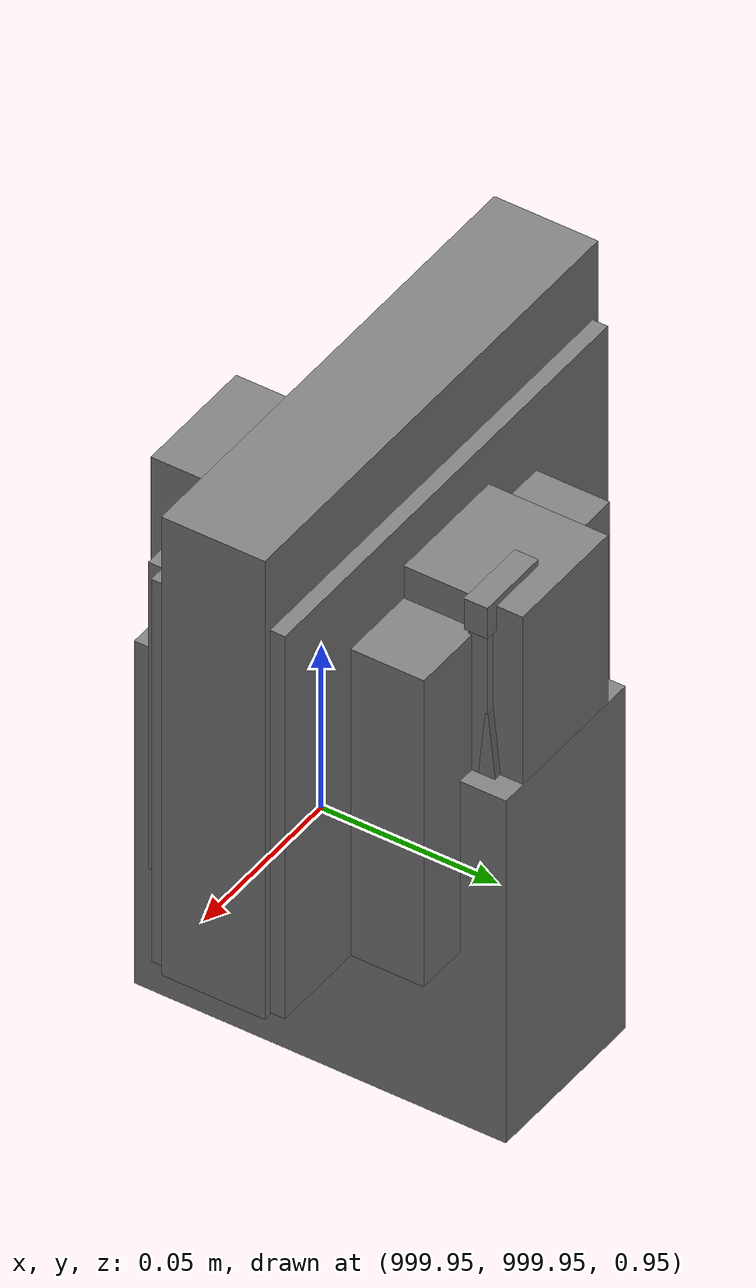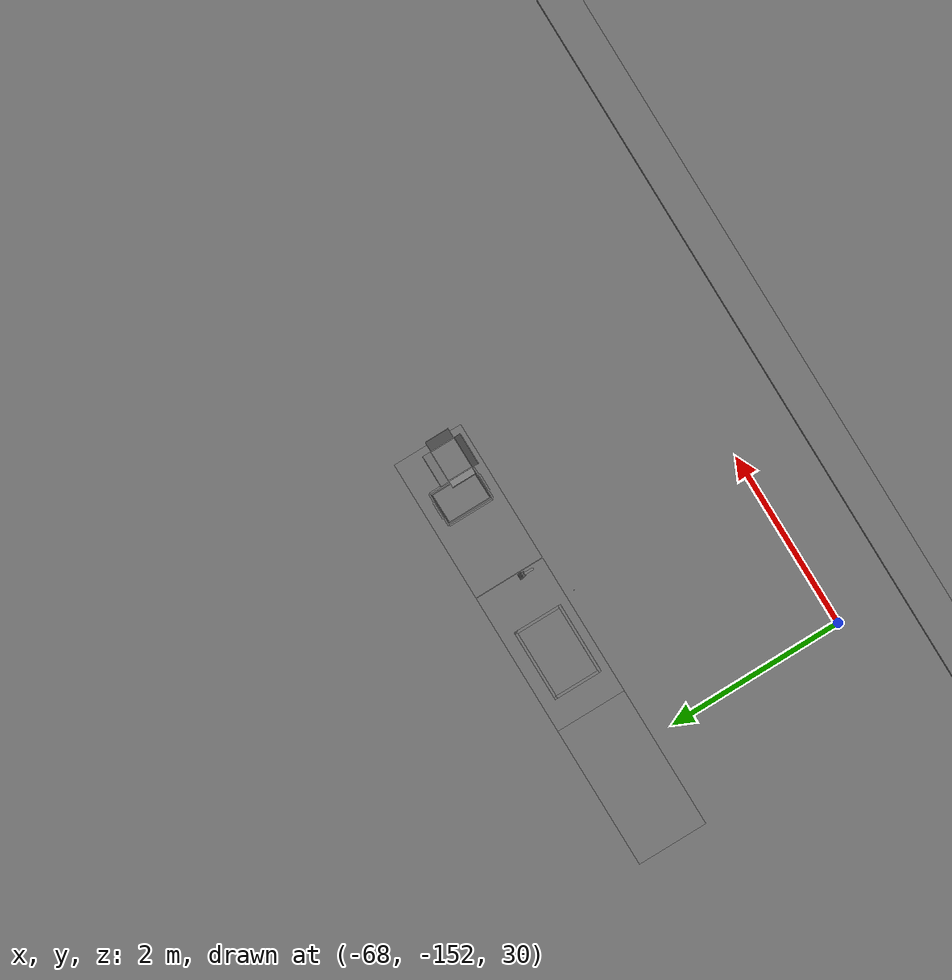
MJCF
<mujoco>
    <option gravity="0.000000000 0.000000000 -9.810000420" timestep="0.0049999999" integrator="implicitfast" density="1.225" viscosity="1.8000001e-05" noslip_iterations="10" iterations="100" sdf_iterations="50">
        <flag multiccd="disable"/>
    </option>
    <size memory="1000M"/>
    <compiler coordinate="local"/>
    <worldbody>
        <light cutoff="30" pos="0 1 1" dir="0 -1 -2"/>
        <light cutoff="30" pos="0 -1 1" dir="0 1 -2"/>
        <body pos="-64.866622925 -149.383972168 30.183746338" euler="89.999984741 89.999946594 0.000000000" name="openloong_gripper_2f85_fix_base_usda_bluebox_01">
            <geom contype="1" conaffinity="1" density="1000" type="box" material="" rgba="0.500000000 0.500000000 0.500000000 1.000000000" solimp="0.899999976 0.949999988 0.001000000" friction="1.000000000 0.005000000 0.000100000" solref="0.020000000 1.000000000" margin="0" condim="3" group="0" pos="0.276580811 0.187225342 0.000068665" quat="0.707106948 0.000077471 0.707106352 0.000077486" size="0.100000001 0.057999998 0.010000000" name="openloong_gripper_2f85_fix_base_usda_geom_A962B340_3607_4CAB_B4F8_A5DEB269C2CE"/>
            <geom contype="1" conaffinity="1" density="1000" type="box" material="" rgba="0.500000000 0.500000000 0.500000000 1.000000000" solimp="0.899999976 0.949999988 0.001000000" friction="1.000000000 0.005000000 0.000100000" solref="0.020000000 1.000000000" margin="0" condim="3" group="0" pos="0.000000000 0.002883911 0.000000000" quat="0.999999881 0.000000000 0.000000000 0.000000000" size="0.254000008 0.003000000 0.172000006" name="openloong_gripper_2f85_fix_base_usda_geom_1CF8B3DB_E445_431A_A701_C343FFE65B24"/>
            <geom contype="1" conaffinity="1" density="1000" type="box" material="" rgba="0.500000000 0.500000000 0.500000000 1.000000000" solimp="0.899999976 0.949999988 0.001000000" friction="1.000000000 0.005000000 0.000100000" solref="0.020000000 1.000000000" margin="0" condim="3" group="0" pos="0.000000000 0.124874115 0.173484802" quat="0.999796331 0.020176515 -0.000000015 0.000000030" size="0.259999990 0.119999997 0.007000000" name="openloong_gripper_2f85_fix_base_usda_geom_6608388E_AA45_43E3_939F_DA10C1CE674A"/>
            <geom contype="1" conaffinity="1" density="1000" type="box" material="" rgba="0.500000000 0.500000000 0.500000000 1.000000000" solimp="0.899999976 0.949999988 0.001000000" friction="1.000000000 0.005000000 0.000100000" solref="0.020000000 1.000000000" margin="0" condim="3" group="0" pos="0.000000000 0.124874115 -0.173469543" quat="0.999796331 -0.020176545 -0.000000015 0.000000000" size="0.259999990 0.119999997 0.007000000" name="openloong_gripper_2f85_fix_base_usda_geom_B7FC5B5C_BE2D_49DF_A370_4B0A0F5E9D93"/>
            <geom contype="1" conaffinity="1" density="1000" type="box" material="" rgba="0.500000000 0.500000000 0.500000000 1.000000000" solimp="0.899999976 0.949999988 0.001000000" friction="1.000000000 0.005000000 0.000100000" solref="0.020000000 1.000000000" margin="0" condim="3" group="0" pos="0.000000000 0.214008331 0.188980103" quat="0.999912977 0.013176724 0.000000015 0.000000000" size="0.259999990 0.029999999 0.012500000" name="openloong_gripper_2f85_fix_base_usda_geom_BB877B0F_1580_4D98_B58E_70652481C97B"/>
            <geom contype="1" conaffinity="1" density="1000" type="box" material="" rgba="0.500000000 0.500000000 0.500000000 1.000000000" solimp="0.899999976 0.949999988 0.001000000" friction="1.000000000 0.005000000 0.000100000" solref="0.020000000 1.000000000" margin="0" condim="3" group="0" pos="-0.258361816 0.125289917 0.001876831" quat="0.702796936 -0.020792112 0.710783124 0.020769298" size="0.189999998 0.119999997 0.009000000" name="openloong_gripper_2f85_fix_base_usda_geom_2B2BCCD2_0787_4808_B5A0_2751283C6062"/>
            <geom contype="1" conaffinity="1" density="1000" type="box" material="" rgba="0.500000000 0.500000000 0.500000000 1.000000000" solimp="0.899999976 0.949999988 0.001000000" friction="1.000000000 0.005000000 0.000100000" solref="0.020000000 1.000000000" margin="0" condim="3" group="0" pos="0.000000000 0.214008331 -0.188980103" quat="0.999912977 -0.013176769 0.000000030 0.000000015" size="0.259999990 0.029999999 0.012500000" name="openloong_gripper_2f85_fix_base_usda_geom_C9F9795B_CF7F_4530_BF5C_05A01D5C53D5"/>
            <geom contype="1" conaffinity="1" density="1000" type="box" material="" rgba="0.500000000 0.500000000 0.500000000 1.000000000" solimp="0.899999976 0.949999988 0.001000000" friction="1.000000000 0.005000000 0.000100000" solref="0.020000000 1.000000000" margin="0" condim="3" group="0" pos="-0.276611328 0.187225342 0.000068665" quat="0.707106650 0.000077441 0.707106709 0.000077456" size="0.100000001 0.057999998 0.010000000" name="openloong_gripper_2f85_fix_base_usda_geom_145FA3E6_BE04_4A39_9DF2_C82ED92B759C"/>
            <geom contype="1" conaffinity="1" density="1000" type="box" material="" rgba="0.500000000 0.500000000 0.500000000 1.000000000" solimp="0.899999976 0.949999988 0.001000000" friction="1.000000000 0.005000000 0.000100000" solref="0.020000000 1.000000000" margin="0" condim="3" group="0" pos="0.258331299 0.125289917 0.001876831" quat="0.702851415 0.018856421 0.710823774 -0.019329369" size="0.189999998 0.119999997 0.009000000" name="openloong_gripper_2f85_fix_base_usda_geom_761DBE81_015F_4F61_A169_CBA69AFBA450"/>
            <freejoint name="openloong_gripper_2f85_fix_base_usda_bluebox_01_joint"/>
            <site size="0.005000000 0.005000000 0.005000000" rgba="0.500000000 0.500000000 0.500000000 1.000000000" pos="0.000000000 0.000000000 0.000000000" quat="0.999961913 0.008726534 0.000000000 0.000000000" group="0" type="sphere" name="openloong_gripper_2f85_fix_base_usda_bluebox_01site"/>
        </body>
        <body pos="-64.496299744 -149.491867065 30.235729218" euler="0.000000000 0.000000000 89.999946594" name="openloong_gripper_2f85_fix_base_usda_cardboardbox_01">
            <geom contype="1" conaffinity="1" density="1000" type="box" material="" rgba="0.500000000 0.500000000 0.500000000 1.000000000" solimp="0.899999976 0.949999988 0.001000000" friction="1.000000000 0.005000000 0.000100000" solref="0.020000000 1.000000000" margin="0" condim="3" group="0" pos="-0.003166199 -0.004086494 0.005052090" quat="1.000000000 0.000000000 0.000000000 0.000000000" size="0.142499998 0.177500010 0.005000000" name="openloong_gripper_2f85_fix_base_usda_geom_8F30BD16_6FA8_4DF0_8274_3E8E6EEFC211"/>
            <geom contype="1" conaffinity="1" density="1000" type="box" material="" rgba="0.500000000 0.500000000 0.500000000 1.000000000" solimp="0.899999976 0.949999988 0.001000000" friction="1.000000000 0.005000000 0.000100000" solref="0.020000000 1.000000000" margin="0" condim="3" group="0" pos="-0.003166199 0.170316696 0.150570869" quat="1.000000000 0.000000000 0.000000000 0.000000000" size="0.142499998 0.005000000 0.149999991" name="openloong_gripper_2f85_fix_base_usda_geom_C3093FEF_A58B_42BA_873D_5C0CDAEB375F"/>
            <geom contype="1" conaffinity="1" density="1000" type="box" material="" rgba="0.500000000 0.500000000 0.500000000 1.000000000" solimp="0.899999976 0.949999988 0.001000000" friction="1.000000000 0.005000000 0.000100000" solref="0.020000000 1.000000000" margin="0" condim="3" group="0" pos="-0.147399902 -0.005307198 0.150570869" quat="1.000000000 0.000000000 0.000000000 0.000000000" size="0.005000000 0.177500010 0.149999991" name="openloong_gripper_2f85_fix_base_usda_geom_AEE43F4C_B2E7_443E_8E1F_E450EF130796"/>
            <geom contype="1" conaffinity="1" density="1000" type="box" material="" rgba="0.500000000 0.500000000 0.500000000 1.000000000" solimp="0.899999976 0.949999988 0.001000000" friction="1.000000000 0.005000000 0.000100000" solref="0.020000000 1.000000000" margin="0" condim="3" group="0" pos="0.140275955 -0.005307198 0.150570869" quat="1.000000000 0.000000000 0.000000000 0.000000000" size="0.005000000 0.177500010 0.149999991" name="openloong_gripper_2f85_fix_base_usda_geom_868D533D_980A_4E5E_AAE6_9FB447BCD1AB"/>
            <geom contype="1" conaffinity="1" density="1000" type="box" material="" rgba="0.500000000 0.500000000 0.500000000 1.000000000" solimp="0.899999976 0.949999988 0.001000000" friction="1.000000000 0.005000000 0.000100000" solref="0.020000000 1.000000000" margin="0" condim="3" group="0" pos="-0.003166199 -0.181550980 0.150570869" quat="1.000000000 0.000000000 0.000000000 0.000000000" size="0.142499998 0.005000000 0.149999991" name="openloong_gripper_2f85_fix_base_usda_geom_D575CDA2_52B5_4BD1_A954_16F078AAFF80"/>
            <freejoint name="openloong_gripper_2f85_fix_base_usda_cardboardbox_01_joint"/>
            <site size="0.005000000 0.005000000 0.005000000" rgba="0.500000000 0.500000000 0.500000000 1.000000000" pos="0.000000000 0.000000000 0.000000000" quat="0.999961913 0.008726535 0.000000000 0.000000000" group="0" type="sphere" name="openloong_gripper_2f85_fix_base_usda_site_A9C3A05F_BA1C_4EE9_94FA_2128EA5BB02C"/>
            <body pos="0.139160156 -0.004048347 0.301930904" euler="-179.999954224 49.383502960 179.999954224" name="openloong_gripper_2f85_fix_base_usda_A1_006">
                <geom contype="1" conaffinity="1" density="1000" type="box" material="" rgba="0.500000000 0.500000000 0.500000000 1.000000000" solimp="0.899999976 0.949999988 0.001000000" friction="1.000000000 0.005000000 0.000100000" solref="0.020000000 1.000000000" margin="0" condim="3" group="0" pos="-0.071587563 0.000009537 0.001745224" quat="0.999999881 0.000000000 0.000000000 0.000000000" size="0.071249999 0.179999992 0.002500000" name="openloong_gripper_2f85_fix_base_usda_geom_1D3D1F35_DAFB_41A9_BC51_8F9200610A4B"/>
                <joint armature="0" stiffness="0.07" damping="0.0099999998" axis="0.000000 1.000000 0.000000" type="hinge" name="openloong_gripper_2f85_fix_base_usda_A1_006"/>
            </body>
            <body pos="-0.145902634 -0.004086494 0.301938057" euler="-180.000000000 -60.000011444 -180.000000000" name="openloong_gripper_2f85_fix_base_usda_A2_006">
                <geom contype="1" conaffinity="1" density="1000" type="box" material="" rgba="0.500000000 0.500000000 0.500000000 1.000000000" solimp="0.899999976 0.949999988 0.001000000" friction="1.000000000 0.005000000 0.000100000" solref="0.020000000 1.000000000" margin="0" condim="3" group="0" pos="0.071268082 0.000009537 0.002717972" quat="0.000002921 0.000000000 -0.000000030 0.999999881" size="0.071249999 0.179999992 0.002500000" name="openloong_gripper_2f85_fix_base_usda_geom_22516CCB_10FD_442D_B133_E378CD4BEC46"/>
                <joint armature="0" stiffness="0.07" damping="0.0099999998" axis="0.000000 1.000000 0.000000" type="hinge" name="openloong_gripper_2f85_fix_base_usda_A2_006"/>
            </body>
            <body pos="-0.003385544 0.175991058 0.301930904" euler="-125.858116150 -0.000004561 0.000002331" name="openloong_gripper_2f85_fix_base_usda_B2_006">
                <geom contype="1" conaffinity="1" density="1000" type="box" material="" rgba="0.500000000 0.500000000 0.500000000 1.000000000" solimp="0.899999976 0.949999988 0.001000000" friction="1.000000000 0.005000000 0.000100000" solref="0.020000000 1.000000000" margin="0" condim="3" group="0" pos="0.000009537 -0.070939064 -0.002470016" quat="0.999614120 0.027776197 -0.000000015 0.000000030" size="0.137500003 0.064999998 0.005000000" name="openloong_gripper_2f85_fix_base_usda_geom_45AC0EC7_AF89_4572_B73F_CBF71D04443B"/>
                <joint armature="0" stiffness="0.07" damping="0.0099999998" axis="1.000000 0.000000 0.000000" type="hinge" name="openloong_gripper_2f85_fix_base_usda_B2_006"/>
            </body>
            <body pos="-0.003385544 -0.184140205 0.301938057" euler="147.805557251 0.000000000 0.000000000" name="openloong_gripper_2f85_fix_base_usda_B1_006">
                <geom contype="1" conaffinity="1" density="1000" type="box" material="" rgba="0.500000000 0.500000000 0.500000000 1.000000000" solimp="0.899999976 0.949999988 0.001000000" friction="1.000000000 0.005000000 0.000100000" solref="0.020000000 1.000000000" margin="0" condim="3" group="0" pos="-0.000028610 0.070202351 -0.002703667" quat="0.999614179 -0.027776167 0.000000000 0.000000000" size="0.137500003 0.064999998 0.005000000" name="openloong_gripper_2f85_fix_base_usda_geom_E9DFCD21_D8D4_4758_9506_79AFD737CDF2"/>
                <joint armature="0" stiffness="0.07" damping="0.0099999998" axis="1.000000 0.000000 0.000000" type="hinge" name="openloong_gripper_2f85_fix_base_usda_B1_006"/>
            </body>
        </body>
        <body pos="-65.882858276 -149.481979370 30.229999542" euler="-64.487716675 0.000000000 0.000000000" name="openloong_gripper_2f85_fix_base_usda_Barcode">
            <geom contype="1" conaffinity="1" density="1000" type="box" material="" rgba="0.500000000 0.500000000 0.500000000 1.000000000" solimp="0.899999976 0.949999988 0.001000000" friction="1.000000000 0.005000000 0.000100000" solref="0.020000000 1.000000000" margin="0" condim="3" group="0" pos="0.000000000 0.013038635 0.001419067" quat="0.000000000 0.000000000 0.000000000 1.000000119" size="0.034000002 0.010000000 0.017999999" name="openloong_gripper_2f85_fix_base_usda_geom_BD9A1A79_8EE7_42BB_9E5C_AF4F5B5507EB"/>
            <geom contype="1" conaffinity="1" density="1000" type="box" material="" rgba="0.500000000 0.500000000 0.500000000 1.000000000" solimp="0.899999976 0.949999988 0.001000000" friction="1.000000000 0.005000000 0.000100000" solref="0.020000000 1.000000000" margin="0" condim="3" group="0" pos="0.000000000 -0.035301208 -0.007095337" quat="0.000000000 0.000000000 -0.043619365 0.999048233" size="0.028999999 0.010000000 0.020000000" name="openloong_gripper_2f85_fix_base_usda_geom_368275EE_0936_4D3F_820B_8E9A718F7F70"/>
            <geom contype="1" conaffinity="1" density="1000" type="box" material="" rgba="0.500000000 0.500000000 0.500000000 1.000000000" solimp="0.899999976 0.949999988 0.001000000" friction="1.000000000 0.005000000 0.000100000" solref="0.020000000 1.000000000" margin="0" condim="3" group="0" pos="0.000000000 -0.043411255 -0.011749268" quat="0.922262907 0.386563420 0.000000000 0.000000000" size="0.026000001 0.010000000 0.020000000" name="openloong_gripper_2f85_fix_base_usda_geom_8BFC1FAA_300D_4CCE_A5A3_64279D395B20"/>
            <geom contype="1" conaffinity="1" density="1000" type="box" material="" rgba="0.500000000 0.500000000 0.500000000 1.000000000" solimp="0.899999976 0.949999988 0.001000000" friction="1.000000000 0.005000000 0.000100000" solref="0.020000000 1.000000000" margin="0" condim="3" group="0" pos="0.000000000 -0.016967773 -0.031860352" quat="0.000000000 0.000000000 0.000000000 1.000000119" size="0.008000000 0.010000000 0.013000000" name="openloong_gripper_2f85_fix_base_usda_geom_8A0FADBE_6860_4D09_992F_493D48A5820F"/>
            <geom contype="1" conaffinity="1" density="1000" type="box" material="" rgba="0.500000000 0.500000000 0.500000000 1.000000000" solimp="0.899999976 0.949999988 0.001000000" friction="1.000000000 0.005000000 0.000100000" solref="0.020000000 1.000000000" margin="0" condim="3" group="0" pos="0.000000000 -0.001869202 0.000312805" quat="0.953716993 0.300705761 0.000000000 0.000000000" size="0.032000002 0.010000000 0.018999999" name="openloong_gripper_2f85_fix_base_usda_geom_A288B092_3FA8_4458_84A8_E5BC36F2C455"/>
            <geom contype="1" conaffinity="1" density="1000" type="box" material="" rgba="0.500000000 0.500000000 0.500000000 1.000000000" solimp="0.899999976 0.949999988 0.001000000" friction="1.000000000 0.005000000 0.000100000" solref="0.020000000 1.000000000" margin="0" condim="3" group="0" pos="0.000000000 -0.019531250 -0.003173828" quat="0.953716993 0.300705761 0.000000000 0.000000000" size="0.030999999 0.010000000 0.020000000" name="openloong_gripper_2f85_fix_base_usda_geom_F4AA5571_4BB5_4175_81E1_B0B5BA9AA70C"/>
            <geom contype="1" conaffinity="1" density="1000" type="box" material="" rgba="0.500000000 0.500000000 0.500000000 1.000000000" solimp="0.899999976 0.949999988 0.001000000" friction="1.000000000 0.005000000 0.000100000" solref="0.020000000 1.000000000" margin="0" condim="3" group="0" pos="0.000000000 -0.035301208 -0.007095337" quat="0.953716993 0.300705761 0.000000000 0.000000000" size="0.028999999 0.010000000 0.020000000" name="openloong_gripper_2f85_fix_base_usda_geom_908080DD_51AD_46E3_9719_86679A8D0993"/>
            <geom contype="1" conaffinity="1" density="1000" type="box" material="" rgba="0.500000000 0.500000000 0.500000000 1.000000000" solimp="0.899999976 0.949999988 0.001000000" friction="1.000000000 0.005000000 0.000100000" solref="0.020000000 1.000000000" margin="0" condim="3" group="0" pos="0.000000000 -0.042617798 -0.071121216" quat="0.000000000 0.000000000 0.000000000 1.000000119" size="0.013000000 0.021000000 0.059999999" name="openloong_gripper_2f85_fix_base_usda_geom_38EC132C_4FE6_47B8_BD66_C8DB1329A4F6"/>
            <freejoint name="openloong_gripper_2f85_fix_base_usda_Barcode_joint"/>
            <site size="0.005000000 0.005000000 0.005000000" rgba="0.500000000 0.500000000 0.500000000 1.000000000" pos="0.000000000 0.000000000 0.000000000" quat="1.000000000 0.000000000 0.000000000 0.000000000" group="0" type="sphere" name="openloong_gripper_2f85_fix_base_usda_Barcode_site"/>
        </body>
        <body pos="-66.745018005 -149.392349243 30.184000015" euler="0.000000000 0.000000000 89.999946594" name="[22332606261930]_Basket_01">
            <geom contype="1" conaffinity="1" density="1000" type="box" material="" rgba="0.500000000 0.500000000 0.500000000 1.000000000" solimp="0.899999976 0.949999988 0.001000000" friction="1.000000000 0.005000000 0.000100000" solref="0.020000000 1.000000000" margin="0" condim="3" group="0" pos="-0.052425385 0.389207840 0.089787483" quat="0.707107008 0.000000000 0.000000000 0.707106411" size="0.014249999 0.014249999 0.059999999" name="[22332606261930]_geom_468BB90F_FEE0_4117_AEE9_E208CACF9699"/>
            <geom contype="1" conaffinity="1" density="1000" type="box" material="" rgba="0.500000000 0.500000000 0.500000000 1.000000000" solimp="0.899999976 0.949999988 0.001000000" friction="1.000000000 0.005000000 0.000100000" solref="0.020000000 1.000000000" margin="0" condim="3" group="0" pos="0.264015198 -0.133043289 0.089787483" quat="0.707107008 0.000000000 0.000000000 0.707106411" size="0.014249999 0.014249999 0.059999999" name="[22332606261930]_geom_028273EE_C242_4B8B_A394_33FF23704D40"/>
            <geom contype="1" conaffinity="1" density="1000" type="box" material="" rgba="0.500000000 0.500000000 0.500000000 1.000000000" solimp="0.899999976 0.949999988 0.001000000" friction="1.000000000 0.005000000 0.000100000" solref="0.020000000 1.000000000" margin="0" condim="3" group="0" pos="-0.264015198 -0.265548706 0.089793205" quat="0.707107008 0.000000000 0.000000000 0.707106411" size="0.014249999 0.014249999 0.059999999" name="[22332606261930]_geom_A602EA01_6070_4C84_BEA8_117914FE1D75"/>
            <geom contype="1" conaffinity="1" density="1000" type="box" material="" rgba="0.500000000 0.500000000 0.500000000 1.000000000" solimp="0.899999976 0.949999988 0.001000000" friction="1.000000000 0.005000000 0.000100000" solref="0.020000000 1.000000000" margin="0" condim="3" group="0" pos="-0.160263062 -0.389322281 0.089793205" quat="0.707107008 0.000000000 0.000000000 0.707106411" size="0.014249999 0.014249999 0.059999999" name="[22332606261930]_geom_41C2AB03_8BCD_44A5_BE08_E431EFB479DF"/>
            <geom contype="1" conaffinity="1" density="1000" type="box" material="" rgba="0.500000000 0.500000000 0.500000000 1.000000000" solimp="0.899999976 0.949999988 0.001000000" friction="1.000000000 0.005000000 0.000100000" solref="0.020000000 1.000000000" margin="0" condim="3" group="0" pos="0.162265778 -0.389322281 0.089787483" quat="0.707107008 0.000000000 0.000000000 0.707106411" size="0.014249999 0.014249999 0.059999999" name="[22332606261930]_geom_94240793_7D8A_4289_B445_B3D057447ADF"/>
            <geom contype="1" conaffinity="1" density="1000" type="box" material="" rgba="0.500000000 0.500000000 0.500000000 1.000000000" solimp="0.899999976 0.949999988 0.001000000" friction="1.000000000 0.005000000 0.000100000" solref="0.020000000 1.000000000" margin="0" condim="3" group="0" pos="0.264015198 0.389207840 0.089787483" quat="0.707107008 0.000000000 0.000000000 0.707106411" size="0.014249999 0.014249999 0.059999999" name="[22332606261930]_geom_A361C140_A9B5_4F80_8BB4_5C162E480266"/>
            <geom contype="1" conaffinity="1" density="1000" type="box" material="" rgba="0.500000000 0.500000000 0.500000000 1.000000000" solimp="0.899999976 0.949999988 0.001000000" friction="1.000000000 0.005000000 0.000100000" solref="0.020000000 1.000000000" margin="0" condim="3" group="0" pos="-0.264015198 -0.133043289 0.089793205" quat="0.707107008 0.000000000 0.000000000 0.707106411" size="0.014249999 0.014249999 0.059999999" name="[22332606261930]_geom_2E8DA387_CE86_4763_A3B1_29EDF66D81D8"/>
            <geom contype="1" conaffinity="1" density="1000" type="box" material="" rgba="0.500000000 0.500000000 0.500000000 1.000000000" solimp="0.899999976 0.949999988 0.001000000" friction="1.000000000 0.005000000 0.000100000" solref="0.020000000 1.000000000" margin="0" condim="3" group="0" pos="-0.264026642 0.269256592 0.089793205" quat="0.707107008 0.000000000 0.000000000 0.707106411" size="0.014249999 0.014249999 0.059999999" name="[22332606261930]_geom_F29EBE6B_0114_45BD_B5B8_BCA338A22D57"/>
            <geom contype="1" conaffinity="1" density="1000" type="box" material="" rgba="0.500000000 0.500000000 0.500000000 1.000000000" solimp="0.899999976 0.949999988 0.001000000" friction="1.000000000 0.005000000 0.000100000" solref="0.020000000 1.000000000" margin="0" condim="3" group="0" pos="0.054462433 0.389207840 0.089787483" quat="0.707107008 0.000000000 0.000000000 0.707106411" size="0.014249999 0.014249999 0.059999999" name="[22332606261930]_geom_BD2FE41D_1FBF_4EC6_8EBB_0AFE90DACD8E"/>
            <geom contype="1" conaffinity="1" density="1000" type="box" material="" rgba="0.500000000 0.500000000 0.500000000 1.000000000" solimp="0.899999976 0.949999988 0.001000000" friction="1.000000000 0.005000000 0.000100000" solref="0.020000000 1.000000000" margin="0" condim="3" group="0" pos="0.054462433 -0.389322281 0.089787483" quat="0.707107008 0.000000000 0.000000000 0.707106411" size="0.014249999 0.014249999 0.059999999" name="[22332606261930]_geom_E61A5C2C_C20D_4F8F_9C23_56129BCF014C"/>
            <geom contype="1" conaffinity="1" density="1000" type="box" material="" rgba="0.500000000 0.500000000 0.500000000 1.000000000" solimp="0.899999976 0.949999988 0.001000000" friction="1.000000000 0.005000000 0.000100000" solref="0.020000000 1.000000000" margin="0" condim="3" group="0" pos="0.264015198 0.269256592 0.089793205" quat="0.707107008 0.000000000 0.000000000 0.707106411" size="0.014249999 0.014249999 0.059999999" name="[22332606261930]_geom_076AFA27_035C_4A74_8B03_BB15B64838D9"/>
            <geom contype="1" conaffinity="1" density="1000" type="box" material="" rgba="0.500000000 0.500000000 0.500000000 1.000000000" solimp="0.899999976 0.949999988 0.001000000" friction="1.000000000 0.005000000 0.000100000" solref="0.020000000 1.000000000" margin="0" condim="3" group="0" pos="0.264015198 -0.389322281 0.089787483" quat="0.707107008 0.000000000 0.000000000 0.707106411" size="0.014249999 0.014249999 0.059999999" name="[22332606261930]_geom_5124C698_A159_4B85_B4E5_82363B6209D4"/>
            <geom contype="1" conaffinity="1" density="1000" type="box" material="" rgba="0.500000000 0.500000000 0.500000000 1.000000000" solimp="0.899999976 0.949999988 0.001000000" friction="1.000000000 0.005000000 0.000100000" solref="0.020000000 1.000000000" margin="0" condim="3" group="0" pos="0.000000000 0.000000000 0.015998840" quat="0.707107008 0.000000000 0.000000000 0.707106411" size="0.403499991 0.279000014 0.015750000" name="[22332606261930]_geom_A5F334B4_4EC4_49A8_9BA9_6B99539463CC"/>
            <geom contype="1" conaffinity="1" density="1000" type="box" material="" rgba="0.500000000 0.500000000 0.500000000 1.000000000" solimp="0.899999976 0.949999988 0.001000000" friction="1.000000000 0.005000000 0.000100000" solref="0.020000000 1.000000000" margin="0" condim="3" group="0" pos="0.000000000 -0.389476776 0.163619041" quat="0.707107008 0.000000000 0.000000000 0.707106411" size="0.015000000 0.277500004 0.015750000" name="[22332606261930]_geom_BF07C624_F837_43F9_954F_004D61B14CD4"/>
            <geom contype="1" conaffinity="1" density="1000" type="box" material="" rgba="0.500000000 0.500000000 0.500000000 1.000000000" solimp="0.899999976 0.949999988 0.001000000" friction="1.000000000 0.005000000 0.000100000" solref="0.020000000 1.000000000" margin="0" condim="3" group="0" pos="0.162265778 0.389207840 0.089787483" quat="0.707107008 0.000000000 0.000000000 0.707106411" size="0.014249999 0.014249999 0.059999999" name="[22332606261930]_geom_BB59D8F8_F6A3_42E8_BFC0_D913AF414B50"/>
            <geom contype="1" conaffinity="1" density="1000" type="box" material="" rgba="0.500000000 0.500000000 0.500000000 1.000000000" solimp="0.899999976 0.949999988 0.001000000" friction="1.000000000 0.005000000 0.000100000" solref="0.020000000 1.000000000" margin="0" condim="3" group="0" pos="0.000000000 0.389471054 0.163619041" quat="0.707107008 0.000000000 0.000000000 0.707106411" size="0.015000000 0.277500004 0.015750000" name="[22332606261930]_geom_FEF5F6C1_F02F_4F8D_94E4_1A19C685AD75"/>
            <geom contype="1" conaffinity="1" density="1000" type="box" material="" rgba="0.500000000 0.500000000 0.500000000 1.000000000" solimp="0.899999976 0.949999988 0.001000000" friction="1.000000000 0.005000000 0.000100000" solref="0.020000000 1.000000000" margin="0" condim="3" group="0" pos="-0.263511658 0.000000000 0.163619041" quat="0.707107008 0.000000000 0.000000000 0.707106411" size="0.403499991 0.015000000 0.015750000" name="[22332606261930]_geom_99168FCF_E1F8_41F9_8731_E2F3C3090403"/>
            <geom contype="1" conaffinity="1" density="1000" type="box" material="" rgba="0.500000000 0.500000000 0.500000000 1.000000000" solimp="0.899999976 0.949999988 0.001000000" friction="1.000000000 0.005000000 0.000100000" solref="0.020000000 1.000000000" margin="0" condim="3" group="0" pos="-0.264015198 0.141334534 0.089793205" quat="0.707107008 0.000000000 0.000000000 0.707106411" size="0.014249999 0.014249999 0.059999999" name="[22332606261930]_geom_E7F014FC_0921_49F9_AEB5_0D671F20EE5D"/>
            <geom contype="1" conaffinity="1" density="1000" type="box" material="" rgba="0.500000000 0.500000000 0.500000000 1.000000000" solimp="0.899999976 0.949999988 0.001000000" friction="1.000000000 0.005000000 0.000100000" solref="0.020000000 1.000000000" margin="0" condim="3" group="0" pos="0.264015198 -0.265548706 0.089787483" quat="0.707107008 0.000000000 0.000000000 0.707106411" size="0.014249999 0.014249999 0.059999999" name="[22332606261930]_geom_5EF5ADDF_20D5_47DC_9833_1BF9655AEFD8"/>
            <geom contype="1" conaffinity="1" density="1000" type="box" material="" rgba="0.500000000 0.500000000 0.500000000 1.000000000" solimp="0.899999976 0.949999988 0.001000000" friction="1.000000000 0.005000000 0.000100000" solref="0.020000000 1.000000000" margin="0" condim="3" group="0" pos="-0.160263062 0.389207840 0.089787483" quat="0.707107008 0.000000000 0.000000000 0.707106411" size="0.014249999 0.014249999 0.059999999" name="[22332606261930]_geom_1968955F_8B8D_4A3A_BCB6_73FE447281E1"/>
            <geom contype="1" conaffinity="1" density="1000" type="box" material="" rgba="0.500000000 0.500000000 0.500000000 1.000000000" solimp="0.899999976 0.949999988 0.001000000" friction="1.000000000 0.005000000 0.000100000" solref="0.020000000 1.000000000" margin="0" condim="3" group="0" pos="-0.052425385 -0.389322281 0.089787483" quat="0.707107008 0.000000000 0.000000000 0.707106411" size="0.014249999 0.014249999 0.059999999" name="[22332606261930]_geom_A79E8443_C6D2_4D71_BAAE_7018EF429793"/>
            <geom contype="1" conaffinity="1" density="1000" type="box" material="" rgba="0.500000000 0.500000000 0.500000000 1.000000000" solimp="0.899999976 0.949999988 0.001000000" friction="1.000000000 0.005000000 0.000100000" solref="0.020000000 1.000000000" margin="0" condim="3" group="0" pos="-0.264026642 -0.389322281 0.089793205" quat="0.707107008 0.000000000 0.000000000 0.707106411" size="0.014249999 0.014249999 0.059999999" name="[22332606261930]_geom_D765B494_4402_4286_8E65_C80261877B23"/>
            <geom contype="1" conaffinity="1" density="1000" type="box" material="" rgba="0.500000000 0.500000000 0.500000000 1.000000000" solimp="0.899999976 0.949999988 0.001000000" friction="1.000000000 0.005000000 0.000100000" solref="0.020000000 1.000000000" margin="0" condim="3" group="0" pos="0.264015198 0.141334534 0.089787483" quat="0.707107008 0.000000000 0.000000000 0.707106411" size="0.014249999 0.014249999 0.059999999" name="[22332606261930]_geom_F85A5EE2_E395_4EC8_B688_EFC8318A53A8"/>
            <geom contype="1" conaffinity="1" density="1000" type="box" material="" rgba="0.500000000 0.500000000 0.500000000 1.000000000" solimp="0.899999976 0.949999988 0.001000000" friction="1.000000000 0.005000000 0.000100000" solref="0.020000000 1.000000000" margin="0" condim="3" group="0" pos="-0.264015198 0.389207840 0.089793205" quat="0.707107008 0.000000000 0.000000000 0.707106411" size="0.014249999 0.014249999 0.059999999" name="[22332606261930]_geom_2AE44BF4_BE38_4353_9641_9BE78B219F7B"/>
            <geom contype="1" conaffinity="1" density="1000" type="box" material="" rgba="0.500000000 0.500000000 0.500000000 1.000000000" solimp="0.899999976 0.949999988 0.001000000" friction="1.000000000 0.005000000 0.000100000" solref="0.020000000 1.000000000" margin="0" condim="3" group="0" pos="0.264015198 0.004480362 0.089787483" quat="0.707107008 0.000000000 0.000000000 0.707106411" size="0.014249999 0.014249999 0.059999999" name="[22332606261930]_geom_024C140C_659F_48E4_AF3F_9AEA93C36A91"/>
            <geom contype="1" conaffinity="1" density="1000" type="box" material="" rgba="0.500000000 0.500000000 0.500000000 1.000000000" solimp="0.899999976 0.949999988 0.001000000" friction="1.000000000 0.005000000 0.000100000" solref="0.020000000 1.000000000" margin="0" condim="3" group="0" pos="0.263694763 -0.000011444 0.163619041" quat="0.707107008 0.000000000 0.000000000 0.707106411" size="0.403499991 0.015000000 0.015750000" name="[22332606261930]_geom_D37B5A12_EF28_4080_9C07_1EEA4F337D30"/>
            <geom contype="1" conaffinity="1" density="1000" type="box" material="" rgba="0.500000000 0.500000000 0.500000000 1.000000000" solimp="0.899999976 0.949999988 0.001000000" friction="1.000000000 0.005000000 0.000100000" solref="0.020000000 1.000000000" margin="0" condim="3" group="0" pos="-0.264015198 0.004480362 0.089793205" quat="0.707107008 0.000000000 0.000000000 0.707106411" size="0.014249999 0.014249999 0.059999999" name="[22332606261930]_geom_AFEF6407_8B6A_40EF_8E69_C81C1D57AFD8"/>
            <freejoint name="[22332606261930]_joint_BE419249_ABD0_4BD4_8C6B_5B6CF19B8DEA"/>
        </body>
        <body pos="0.000000000 0.000000000 0.000000000" euler="0.000000000 0.000000000 0.000000000" name="Static Objects_Static Objects">
            <geom contype="1" conaffinity="1" density="1000" type="box" material="" rgba="0.500000000 0.500000000 0.500000000 1.000000000" solimp="0.899999976 0.949999988 0.001000000" friction="1.000000000 0.005000000 0.000100000" solref="0.020000000 1.000000000" margin="0" condim="3" group="0" pos="-67.544113159 -149.365814209 29.727830887" quat="0.500000417 0.499999970 0.499999553 0.499999970" size="0.381000012 0.319999993 0.041000001" name="Static Objects_geom_ECB02789_B214_4993_9396_9D6F5DFA677C"/>
            <geom contype="1" conaffinity="1" density="1000" type="box" material="" rgba="0.500000000 0.500000000 0.500000000 1.000000000" solimp="0.899999976 0.949999988 0.001000000" friction="1.000000000 0.005000000 0.000100000" solref="0.020000000 1.000000000" margin="0" condim="3" group="0" pos="-68.239501953 -149.365814209 30.086868286" quat="0.500000417 0.499999970 0.499999553 0.499999970" size="0.370999992 0.039500002 0.745000005" name="Static Objects_geom_7E2712EB_1253_4A10_8280_4EF12831F930"/>
            <geom contype="1" conaffinity="1" density="1000" type="box" material="" rgba="0.500000000 0.500000000 0.500000000 1.000000000" solimp="0.899999976 0.949999988 0.001000000" friction="1.000000000 0.005000000 0.000100000" solref="0.020000000 1.000000000" margin="0" condim="3" group="0" pos="-68.239501953 -149.365814209 30.147235870" quat="0.500000417 0.499999970 0.499999553 0.499999970" size="0.400000006 0.022000000 0.800000012" name="Static Objects_geom_74937E12_6A4F_4CEA_91FF_76E092D30AB4"/>
            <geom contype="1" conaffinity="1" density="1000" type="box" material="" rgba="0.500000000 0.500000000 0.500000000 1.000000000" solimp="0.899999976 0.949999988 0.001000000" friction="1.000000000 0.005000000 0.000100000" solref="0.020000000 1.000000000" margin="0" condim="3" group="0" pos="-68.934890747 -149.365814209 29.727830887" quat="0.500000417 0.499999970 0.499999553 0.499999970" size="0.381000012 0.319999993 0.041000001" name="Static Objects_geom_461D8E5F_F61E_4022_B0C7_50C9D47442A3"/>
            <geom contype="1" conaffinity="1" density="1000" type="box" material="" rgba="0.500000000 0.500000000 0.500000000 1.000000000" solimp="0.899999976 0.949999988 0.001000000" friction="1.000000000 0.005000000 0.000100000" solref="0.020000000 1.000000000" margin="0" condim="3" group="0" pos="-68.239501953 -149.365814209 29.561563492" quat="0.500000417 0.499999970 0.499999553 0.499999970" size="0.020000000 0.022000000 0.660000026" name="Static Objects_geom_77BD76DC_2F62_40DD_8596_1D81B5947E7E"/>
            <geom contype="1" conaffinity="1" density="1000" type="box" material="" rgba="0.500000000 0.500000000 0.500000000 1.000000000" solimp="0.899999976 0.949999988 0.001000000" friction="1.000000000 0.005000000 0.000100000" solref="0.020000000 1.000000000" margin="0" condim="3" group="0" pos="-65.945671082 -149.365814209 29.727830887" quat="0.500000417 0.499999970 0.499999553 0.499999970" size="0.381000012 0.319999993 0.041000001" name="Static Objects_geom_63AEFE76_5D4F_417F_B31E_CF1FCCA0C386"/>
            <geom contype="1" conaffinity="1" density="1000" type="box" material="" rgba="0.500000000 0.500000000 0.500000000 1.000000000" solimp="0.899999976 0.949999988 0.001000000" friction="1.000000000 0.005000000 0.000100000" solref="0.020000000 1.000000000" margin="0" condim="3" group="0" pos="-66.641059875 -149.365814209 30.086868286" quat="0.500000417 0.499999970 0.499999553 0.499999970" size="0.370999992 0.039500002 0.745000005" name="Static Objects_geom_9BE8F8A7_92FF_469C_A7CB_978EBBC850BD"/>
            <geom contype="1" conaffinity="1" density="1000" type="box" material="" rgba="0.500000000 0.500000000 0.500000000 1.000000000" solimp="0.899999976 0.949999988 0.001000000" friction="1.000000000 0.005000000 0.000100000" solref="0.020000000 1.000000000" margin="0" condim="3" group="0" pos="-66.641059875 -149.365814209 30.147235870" quat="0.500000417 0.499999970 0.499999553 0.499999970" size="0.400000006 0.022000000 0.800000012" name="Static Objects_geom_80908CAB_7D2B_4938_9824_D835D9996BCA"/>
            <geom contype="1" conaffinity="1" density="1000" type="box" material="" rgba="0.500000000 0.500000000 0.500000000 1.000000000" solimp="0.899999976 0.949999988 0.001000000" friction="1.000000000 0.005000000 0.000100000" solref="0.020000000 1.000000000" margin="0" condim="3" group="0" pos="-67.336448669 -149.365814209 29.727830887" quat="0.500000417 0.499999970 0.499999553 0.499999970" size="0.381000012 0.319999993 0.041000001" name="Static Objects_geom_6E1BA511_DD9E_40FD_A30B_1993AB330592"/>
            <geom contype="1" conaffinity="1" density="1000" type="box" material="" rgba="0.500000000 0.500000000 0.500000000 1.000000000" solimp="0.899999976 0.949999988 0.001000000" friction="1.000000000 0.005000000 0.000100000" solref="0.020000000 1.000000000" margin="0" condim="3" group="0" pos="-66.641059875 -149.365814209 29.561563492" quat="0.500000417 0.499999970 0.499999553 0.499999970" size="0.020000000 0.022000000 0.660000026" name="Static Objects_geom_0C551CAB_0682_4026_B43D_396965B43413"/>
            <geom contype="1" conaffinity="1" density="1000" type="box" material="" rgba="0.500000000 0.500000000 0.500000000 1.000000000" solimp="0.899999976 0.949999988 0.001000000" friction="1.000000000 0.005000000 0.000100000" solref="0.020000000 1.000000000" margin="0" condim="3" group="0" pos="-64.338577271 -149.365814209 29.727830887" quat="0.500000417 0.499999970 0.499999553 0.499999970" size="0.381000012 0.319999993 0.041000001" name="Static Objects_geom_94694D4A_D2A9_417E_AE66_76608FF57929"/>
            <geom contype="1" conaffinity="1" density="1000" type="box" material="" rgba="0.500000000 0.500000000 0.500000000 1.000000000" solimp="0.899999976 0.949999988 0.001000000" friction="1.000000000 0.005000000 0.000100000" solref="0.020000000 1.000000000" margin="0" condim="3" group="0" pos="-65.033966064 -149.365814209 30.086868286" quat="0.500000417 0.499999970 0.499999553 0.499999970" size="0.370999992 0.039500002 0.745000005" name="Static Objects_geom_51D52C28_4BB9_41DA_9E24_2F7E466E9CF0"/>
            <geom contype="1" conaffinity="1" density="1000" type="box" material="" rgba="0.500000000 0.500000000 0.500000000 1.000000000" solimp="0.899999976 0.949999988 0.001000000" friction="1.000000000 0.005000000 0.000100000" solref="0.020000000 1.000000000" margin="0" condim="3" group="0" pos="-65.033966064 -149.365814209 30.147235870" quat="0.500000417 0.499999970 0.499999553 0.499999970" size="0.400000006 0.022000000 0.800000012" name="Static Objects_geom_903387A4_0E08_489F_9197_7C5817F22744"/>
            <geom contype="1" conaffinity="1" density="1000" type="box" material="" rgba="0.500000000 0.500000000 0.500000000 1.000000000" solimp="0.899999976 0.949999988 0.001000000" friction="1.000000000 0.005000000 0.000100000" solref="0.020000000 1.000000000" margin="0" condim="3" group="0" pos="-65.729354858 -149.365814209 29.727830887" quat="0.500000417 0.499999970 0.499999553 0.499999970" size="0.381000012 0.319999993 0.041000001" name="Static Objects_geom_D55A3344_54B0_4B36_A749_0163E137F417"/>
            <geom contype="1" conaffinity="1" density="1000" type="box" material="" rgba="0.500000000 0.500000000 0.500000000 1.000000000" solimp="0.899999976 0.949999988 0.001000000" friction="1.000000000 0.005000000 0.000100000" solref="0.020000000 1.000000000" margin="0" condim="3" group="0" pos="-65.033966064 -149.365814209 29.561563492" quat="0.500000417 0.499999970 0.499999553 0.499999970" size="0.020000000 0.022000000 0.660000026" name="Static Objects_geom_C4B19873_D987_47EC_BEEA_88A2A3825607"/>
            <geom contype="1" conaffinity="1" density="1000" type="box" material="" rgba="0.500000000 0.500000000 0.500000000 1.000000000" solimp="0.899999976 0.949999988 0.001000000" friction="1.000000000 0.005000000 0.000100000" solref="0.020000000 1.000000000" margin="0" condim="3" group="0" pos="-61.754566193 -137.853729248 33.906845093" quat="0.707107067 0.000000000 0.000000000 0.707106471" size="0.759999990 0.759999990 4.500000000" name="Static Objects_geom_7A981598_2F82_4283_9556_A57BDE8407F6"/>
            <geom contype="1" conaffinity="1" density="1000" type="box" material="" rgba="0.500000000 0.500000000 0.500000000 1.000000000" solimp="0.899999976 0.949999988 0.001000000" friction="1.000000000 0.005000000 0.000100000" solref="0.020000000 1.000000000" margin="0" condim="3" group="0" pos="-57.511135101 -144.927108765 31.707921982" quat="1.000000000 0.000000000 0.000000000 0.000000000" size="0.200000003 8.000000000 2.299999952" name="Static Objects_geom_1805679E_26F2_4AAE_9939_AC515A83361C"/>
            <geom contype="1" conaffinity="1" density="1000" type="box" material="" rgba="0.500000000 0.500000000 0.500000000 1.000000000" solimp="0.899999976 0.949999988 0.001000000" friction="1.000000000 0.005000000 0.000100000" solref="0.020000000 1.000000000" margin="0" condim="3" group="0" pos="-80.517646790 -157.574050903 31.688196182" quat="0.707107067 0.000000000 0.000000000 0.707106471" size="0.600000024 0.600000024 2.299999952" name="Static Objects_geom_7633CCCC_D8C9_471B_91C3_06612BF2AB76"/>
            <geom contype="1" conaffinity="1" density="1000" type="box" material="" rgba="0.500000000 0.500000000 0.500000000 1.000000000" solimp="0.899999976 0.949999988 0.001000000" friction="1.000000000 0.005000000 0.000100000" solref="0.020000000 1.000000000" margin="0" condim="3" group="0" pos="-80.711044312 -147.414932251 31.666158676" quat="1.000000000 0.000000000 0.000000000 0.000000000" size="0.200000003 10.000000000 2.299999952" name="Static Objects_geom_BA5CE006_DDE4_4D69_895C_87E343382C23"/>
            <geom contype="1" conaffinity="1" density="1000" type="box" material="" rgba="0.500000000 0.500000000 0.500000000 1.000000000" solimp="0.899999976 0.949999988 0.001000000" friction="1.000000000 0.005000000 0.000100000" solref="0.020000000 1.000000000" margin="0" condim="3" group="0" pos="-57.687217712 -137.434692383 31.688196182" quat="0.707107067 0.000000000 0.000000000 0.707106471" size="0.600000024 0.600000024 2.299999952" name="Static Objects_geom_79B7229A_A2D8_4AE3_BBC0_32B7FAB7CE7C"/>
            <geom contype="1" conaffinity="1" density="1000" type="box" material="" rgba="0.500000000 0.500000000 0.500000000 1.000000000" solimp="0.899999976 0.949999988 0.001000000" friction="1.000000000 0.005000000 0.000100000" solref="0.020000000 1.000000000" margin="0" condim="3" group="0" pos="-69.537033081 -140.263229370 31.714921951" quat="0.707107067 0.000000000 0.000000000 0.707106471" size="0.759999990 4.500000000 2.299999952" name="Static Objects_geom_A42D396B_420A_4D5A_A31D_4BDD2A080765"/>
            <geom contype="1" conaffinity="1" density="1000" type="box" material="" rgba="0.500000000 0.500000000 0.500000000 1.000000000" solimp="0.899999976 0.949999988 0.001000000" friction="1.000000000 0.005000000 0.000100000" solref="0.020000000 1.000000000" margin="0" condim="3" group="0" pos="-80.073638916 -137.853713989 33.906845093" quat="0.707107067 0.000000000 0.000000000 0.707106471" size="0.759999990 0.759999990 4.500000000" name="Static Objects_geom_2F719A7C_A6E9_429B_81F2_282A0D09B67B"/>
            <geom contype="1" conaffinity="1" density="1000" type="box" material="" rgba="0.500000000 0.500000000 0.500000000 1.000000000" solimp="0.899999976 0.949999988 0.001000000" friction="1.000000000 0.005000000 0.000100000" solref="0.020000000 1.000000000" margin="0" condim="3" group="0" pos="-73.406707764 -155.734664917 31.707921982" quat="1.000000000 0.000000000 0.000000000 0.000000000" size="0.200000003 3.000000000 2.299999952" name="Static Objects_geom_55C233AC_0F2C_40DA_9775_B5F42863E29E"/>
            <geom contype="1" conaffinity="1" density="1000" type="box" material="" rgba="0.500000000 0.500000000 0.500000000 1.000000000" solimp="0.899999976 0.949999988 0.001000000" friction="1.000000000 0.005000000 0.000100000" solref="0.020000000 1.000000000" margin="0" condim="3" group="0" pos="-68.497543335 -137.448257446 31.707921982" quat="0.707107067 0.000000000 0.000000000 0.707106471" size="0.200000003 14.000000000 2.299999952" name="Static Objects_geom_7F5EEE6B_E5AC_411F_AAEE_0AEF090BE062"/>
            <geom contype="1" conaffinity="1" density="1000" type="cylinder" material="" rgba="0.500000000 0.500000000 0.500000000 1.000000000" solimp="0.899999976 0.949999988 0.001000000" friction="1.000000000 0.005000000 0.000100000" solref="0.020000000 1.000000000" margin="0" condim="3" group="0" pos="-68.868522644 -142.134506226 31.711090088" quat="0.707107067 0.000000000 0.000000000 0.707106471" size="0.509999990 2.299999952 1.000000000" name="Static Objects_geom_87579044_F673_4599_95F4_284FD20D084D"/>
            <geom contype="1" conaffinity="1" density="1000" type="plane" material="" rgba="0.500000000 0.500000000 0.500000000 1.000000000" solimp="0.899999976 0.949999988 0.001000000" friction="1.000000000 0.005000000 0.000100000" solref="0.020000000 1.000000000" margin="0" condim="3" group="0" pos="-72.873703003 -147.131927490 29.409669876" quat="1.000000000 0.000000000 0.000000000 0.000000000" size="18.000000000 14.000000000 1.000000000" name="Static Objects_geom_AF47FC29_7106_4D08_87AC_CEF8110E04BB"/>
            <geom contype="1" conaffinity="1" density="1000" type="box" material="" rgba="0.500000000 0.500000000 0.500000000 1.000000000" solimp="0.899999976 0.949999988 0.001000000" friction="1.000000000 0.005000000 0.000100000" solref="0.020000000 1.000000000" margin="0" condim="3" group="0" pos="-79.943580627 -157.782272339 31.707921982" quat="0.707107067 0.000000000 0.000000000 0.707106471" size="0.200000003 7.000000000 2.299999952" name="Static Objects_geom_C818D8AD_1483_4E87_9EF0_0C553735F01C"/>
            <geom contype="1" conaffinity="1" density="1000" type="box" material="" rgba="0.500000000 0.500000000 0.500000000 1.000000000" solimp="0.899999976 0.949999988 0.001000000" friction="1.000000000 0.005000000 0.000100000" solref="0.020000000 1.000000000" margin="0" condim="3" group="0" pos="-65.421028137 -152.903442383 31.707921982" quat="0.707107067 0.000000000 0.000000000 0.707106471" size="0.200000003 7.800000191 2.299999952" name="Static Objects_geom_68F2F5E0_472D_4D76_8E32_317915E0D8F2"/>
            <geom contype="1" conaffinity="1" density="1000" type="box" material="" rgba="0.500000000 0.500000000 0.500000000 1.000000000" solimp="0.899999976 0.949999988 0.001000000" friction="1.000000000 0.005000000 0.000100000" solref="0.020000000 1.000000000" margin="0" condim="3" group="0" pos="-74.776908875 -149.964416504 31.688196182" quat="1.000000000 0.000000000 0.000000000 0.000000000" size="0.600000024 0.409999996 2.299999952" name="Static Objects_geom_C63A86EA_18AD_4E41_BB76_DE146D93AA95"/>
            <geom contype="1" conaffinity="1" density="1000" type="cylinder" material="" rgba="0.500000000 0.500000000 0.500000000 1.000000000" solimp="0.899999976 0.949999988 0.001000000" friction="1.000000000 0.005000000 0.000100000" solref="0.020000000 1.000000000" margin="0" condim="3" group="0" pos="-60.161884308 -142.134506226 31.711090088" quat="0.707107067 0.000000000 0.000000000 0.707106471" size="0.509999990 2.299999952 1.000000000" name="Static Objects_geom_4B6F4C0A_9412_491B_B6E7_A020FF1FBC20"/>
            <geom contype="1" conaffinity="1" density="1000" type="cylinder" material="" rgba="0.500000000 0.500000000 0.500000000 1.000000000" solimp="0.899999976 0.949999988 0.001000000" friction="1.000000000 0.005000000 0.000100000" solref="0.020000000 1.000000000" margin="0" condim="3" group="0" pos="-75.382453918 -149.963455200 31.711090088" quat="0.707107067 0.000000000 0.000000000 0.707106471" size="0.409999996 2.299999952 1.000000000" name="Static Objects_geom_E8F1FB0A_458D_47CC_BD81_B629F7FC0BAD"/>
            <geom contype="1" conaffinity="1" density="1000" type="cylinder" material="" rgba="0.500000000 0.500000000 0.500000000 1.000000000" solimp="0.899999976 0.949999988 0.001000000" friction="1.000000000 0.005000000 0.000100000" solref="0.020000000 1.000000000" margin="0" condim="3" group="0" pos="-74.154960632 -149.963455200 31.711090088" quat="0.707107067 0.000000000 0.000000000 0.707106471" size="0.409999996 2.299999952 1.000000000" name="Static Objects_geom_BDC22F19_6F8A_4F68_87B2_9537CA132224"/>
            <geom contype="1" conaffinity="1" density="1000" type="cylinder" material="" rgba="0.500000000 0.500000000 0.500000000 1.000000000" solimp="0.899999976 0.949999988 0.001000000" friction="1.000000000 0.005000000 0.000100000" solref="0.020000000 1.000000000" margin="0" condim="3" group="0" pos="-77.566612244 -142.134506226 31.711090088" quat="0.707107067 0.000000000 0.000000000 0.707106471" size="0.509999990 2.299999952 1.000000000" name="Static Objects_geom_5A7FE4A3_8F83_4945_94FD_23D7FE786EE1"/>
        </body>
        <body pos="-65.798164368 -148.831115723 31.166105270" euler="101.220092773 55.472892761 -95.838523865" mocap="true" name="spotlight1_SpotLight"/>
        <body pos="1000.000000000 1000.000000000 1.000000000" euler="0.000000000 0.000000000 180.000000000" name="openloong_gripper_2f85_fix_base_usda_cpu_fan">
            <geom contype="1" conaffinity="1" density="1000" type="box" material="" rgba="0.500000000 0.500000000 0.500000000 1.000000000" solimp="0.899999976 0.949999988 0.001000000" friction="1.000000000 0.005000000 0.000100000" solref="0.020000000 1.000000000" margin="0" condim="3" group="0" pos="0.000000000 0.000000000 0.070034981" quat="0.000000000 0.000000000 0.000000000 1.000000000" size="0.070700005 0.014699999 0.070700005" name="openloong_gripper_2f85_fix_base_usda_geom_6CE7248C_C68D_4242_BDF4_95B50F22ED4B"/>
            <freejoint name="openloong_gripper_2f85_fix_base_usda_cpu_fan_joint"/>
            <site size="0.005000000 0.005000000 0.005000000" rgba="0.500000000 0.500000000 0.500000000 1.000000000" pos="0.000000000 0.000000000 0.000000000" quat="0.999961913 0.008726535 0.000000000 0.000000000" group="0" type="sphere" name="openloong_gripper_2f85_fix_base_usda_cpu_fancsite"/>
        </body>
        <body pos="1000.000000000 1000.000000000 1.000000000" euler="0.000000000 0.000000000 180.000000000" name="openloong_gripper_2f85_fix_base_usda_wifi_box">
            <geom contype="1" conaffinity="1" density="1000" type="box" material="" rgba="0.500000000 0.500000000 0.500000000 1.000000000" solimp="0.899999976 0.949999988 0.001000000" friction="1.000000000 0.005000000 0.000100000" solref="0.020000000 1.000000000" margin="0" condim="3" group="0" pos="0.000000000 0.000000000 0.058978677" quat="0.000000000 0.000000047 0.000000000 1.000000000" size="0.068499997 0.018999999 0.059000000" name="openloong_gripper_2f85_fix_base_usda_geom_C398B9E9_7BD4_46FE_A60D_CABC88448930"/>
            <freejoint name="openloong_gripper_2f85_fix_base_usda_wifi_box_joint"/>
            <site size="0.005000000 0.005000000 0.005000000" rgba="0.500000000 0.500000000 0.500000000 1.000000000" pos="0.000000000 0.000000000 0.000000000" quat="0.999961913 0.008726500 0.000000000 0.000000000" group="0" type="sphere" name="openloong_gripper_2f85_fix_base_usda_wifi_boxsite"/>
        </body>
        <body pos="1000.000000000 1000.000000000 1.000000000" euler="0.000011953 0.000005123 -179.999984741" name="openloong_gripper_2f85_fix_base_usda_intel_box">
            <geom contype="1" conaffinity="1" density="1000" type="box" material="" rgba="0.500000000 0.500000000 0.500000000 1.000000000" solimp="0.899999976 0.949999988 0.001000000" friction="1.000000000 0.005000000 0.000100000" solref="0.020000000 1.000000000" margin="0" condim="3" group="0" pos="0.000000000 -0.000067139 0.000082284" quat="0.707106709 0.000000225 0.000000253 0.707106650" size="0.052800003 0.025300000 0.052800003" name="openloong_gripper_2f85_fix_base_usda_geom_3615E33D_D73D_4774_ADD3_DAB19C6DD161"/>
            <freejoint name="openloong_gripper_2f85_fix_base_usda_intel_box_joint"/>
            <site size="0.005000000 0.005000000 0.005000000" rgba="0.500000000 0.500000000 0.500000000 1.000000000" pos="0.000000000 0.000000000 0.000000000" quat="0.999961913 0.008726500 0.000000000 0.000000000" group="0" type="sphere" name="openloong_gripper_2f85_fix_base_usda_intel_boxsite"/>
        </body>
        <body pos="1000.000000000 999.999938965 1.000000000" euler="0.000000000 0.000000000 180.000000000" name="openloong_gripper_2f85_fix_base_usda_intelcore_i5">
            <geom contype="1" conaffinity="1" density="1000" type="box" material="" rgba="0.500000000 0.500000000 0.500000000 1.000000000" solimp="0.899999976 0.949999988 0.001000000" friction="1.000000000 0.005000000 0.000100000" solref="0.020000000 1.000000000" margin="0" condim="3" group="0" pos="0.000000000 0.000000000 0.051722717" quat="0.707106709 0.000000000 0.000000000 -0.707106769" size="0.052800000 0.018080002 0.052800000" name="openloong_gripper_2f85_fix_base_usda_geom_FD3FE9EB_51AA_4F27_ABF1_510D09BFFD37"/>
            <freejoint name="openloong_gripper_2f85_fix_base_usda_intelcore_i5_joint"/>
            <site size="0.005000000 0.005000000 0.005000000" rgba="0.500000000 0.500000000 0.500000000 1.000000000" pos="0.000000000 0.000000000 0.000000000" quat="0.999961913 0.008726534 0.000000000 0.000000000" group="0" type="sphere" name="openloong_gripper_2f85_fix_base_usda_intelcore_i5site"/>
        </body>
        <body pos="-65.900177002 -149.643234253 31.166437149" euler="-46.692535400 70.542884827 -126.047393799" mocap="true" name="spotlight2_SpotLight"/>
        <body pos="1000.000000000 1000.000000000 1.000000000" euler="0.000000000 0.000000000 180.000000000" name="openloong_gripper_2f85_fix_base_usda_battery_01">
            <geom contype="1" conaffinity="1" density="1000" type="box" material="" rgba="0.500000000 0.500000000 0.500000000 1.000000000" solimp="0.899999976 0.949999988 0.001000000" friction="1.000000000 0.005000000 0.000100000" solref="0.020000000 1.000000000" margin="0" condim="3" group="0" pos="-0.011123657 -0.041940309 0.101691343" quat="1.000000000 0.000000000 0.000000000 0.000000000" size="0.010800000 0.003375000 0.004725000" name="openloong_gripper_2f85_fix_base_usda_geom_F1A781B0_FF7A_4A3E_B5A8_5716429AFC04"/>
            <geom contype="1" conaffinity="1" density="1000" type="box" material="" rgba="0.500000000 0.500000000 0.500000000 1.000000000" solimp="0.899999976 0.949999988 0.001000000" friction="1.000000000 0.005000000 0.000100000" solref="0.020000000 1.000000000" margin="0" condim="3" group="0" pos="-0.010876465 -0.044247437 0.047066893" quat="0.998702705 -0.050920475 0.000000000 0.000000000" size="0.009450001 0.002700000 0.024975000" name="openloong_gripper_2f85_fix_base_usda_geom_1488A095_D9F4_4916_87B0_8B6F3205DFC2"/>
            <geom contype="1" conaffinity="1" density="1000" type="box" material="" rgba="0.500000000 0.500000000 0.500000000 1.000000000" solimp="0.899999976 0.949999988 0.001000000" friction="1.000000000 0.005000000 0.000100000" solref="0.020000000 1.000000000" margin="0" condim="3" group="0" pos="-0.001235962 -0.000659180 0.047381196" quat="1.000000000 0.000000000 0.000000000 0.000000000" size="0.039420001 0.039150000 0.047250003" name="openloong_gripper_2f85_fix_base_usda_geom_50F2C97C_8397_487F_B2DE_4B511A396EFD"/>
            <geom contype="1" conaffinity="1" density="1000" type="box" material="" rgba="0.500000000 0.500000000 0.500000000 1.000000000" solimp="0.899999976 0.949999988 0.001000000" friction="1.000000000 0.005000000 0.000100000" solref="0.020000000 1.000000000" margin="0" condim="3" group="0" pos="-0.010876465 -0.039138794 0.009851727" quat="1.000000000 0.000000000 0.000000000 0.000000000" size="0.009450001 0.010800000 0.013500000" name="openloong_gripper_2f85_fix_base_usda_geom_1131D105_B1E1_486F_A62B_DD8053578D4A"/>
            <geom contype="1" conaffinity="1" density="1000" type="box" material="" rgba="0.500000000 0.500000000 0.500000000 1.000000000" solimp="0.899999976 0.949999988 0.001000000" friction="1.000000000 0.005000000 0.000100000" solref="0.020000000 1.000000000" margin="0" condim="3" group="0" pos="-0.010876465 -0.041528322 0.071508206" quat="1.000000000 0.000000000 0.000000000 0.000000000" size="0.009450001 0.002700000 0.027000001" name="openloong_gripper_2f85_fix_base_usda_geom_5107A44E_D137_4F53_9242_C43D2EC145C2"/>
            <freejoint name="openloong_gripper_2f85_fix_base_usda_battery_01_joint"/>
            <site size="0.005000000 0.005000000 0.005000000" rgba="0.500000000 0.500000000 0.500000000 1.000000000" pos="0.000000000 0.000000000 0.000000000" quat="0.999961913 0.008726500 0.000000000 0.000000000" group="0" type="sphere" name="openloong_gripper_2f85_fix_base_usda_battery_01site"/>
        </body>
        <body pos="-65.955070496 -149.309448242 31.171602249" euler="66.867515564 -31.521574020 -138.132812500" mocap="true" name="spotlight4_SpotLight"/>
        <body pos="-66.291030884 -149.869689941 29.018842697" euler="0.000000000 0.000000000 89.999946594" mocap="true" name="openloong_gripper_2f85_fix_base_usda_leftHandMocap"/>
        <body pos="-66.291030884 -149.869689941 29.018842697" euler="0.000000000 0.000000000 89.999946594" mocap="true" name="openloong_gripper_2f85_fix_base_usda_rightHandMocap"/>
        <body pos="-66.291030884 -149.869689941 30.218843460" euler="0.000000000 0.000000000 89.999946594" name="openloong_gripper_2f85_fix_base_usda_base_link">
            <geom contype="1" conaffinity="1" density="1000" type="mesh" material="" rgba="0.783999979 0.783999979 0.783999979 1.000000000" solimp="0.899999976 0.949999988 0.001000000" friction="1.000000000 0.005000000 0.000100000" solref="0.020000000 1.000000000" margin="0" condim="3" group="3" mesh="base_link" pos="0.000000000 0.000000000 0.000000000" quat="1.000000000 0.000000000 0.000000000 0.000000000" size="1.000000000 1.000000000 1.000000000" name="openloong_gripper_2f85_fix_base_usda__geom_7_E5CBBF2B_032F_4086_A9A8_8D303EA08752"/>
            <site size="0.005000000 0.005000000 0.005000000" rgba="0.500000000 0.500000000 0.500000000 1.000000000" pos="0.000000000 0.000000000 0.000000000" quat="1.000000000 0.000000000 0.000000000 0.000000000" group="0" type="sphere" name="openloong_gripper_2f85_fix_base_usda_imu"/>
            <inertial mass="22.447001" pos="-0.005664100 -0.001336700 0.238289997" diaginertia="0.374352545 0.277180195 0.220617250" quat="0.999247074 0.035235517 -0.015086859 0.006023135"/>
            <body pos="0.000000000 0.000000000 0.299997330" euler="0.000000000 0.000000000 0.000000000" name="openloong_gripper_2f85_fix_base_usda_dummy_body">
                <geom contype="1" conaffinity="1" density="1000" type="sphere" material="" rgba="0.783999979 0.783999979 0.783999979 1.000000000" solimp="0.899999976 0.949999988 0.001000000" friction="1.000000000 0.005000000 0.000100000" solref="0.020000000 1.000000000" margin="0" condim="3" group="3" pos="0.000000000 0.000000000 0.000000000" quat="1.000000000 0.000000000 0.000000000 0.000000000" size="0.010000000 0.000000000 0.000000000" name="openloong_gripper_2f85_fix_base_usda__geom_8_646DAE02_53BA_4238_A572_1598FCAECEC2"/>
                <joint armature="0.0099999998" stiffness="0" damping="0.1" axis="0.000000 0.000000 1.000000" type="hinge" name="openloong_gripper_2f85_fix_base_usda_dummy_joint"/>
                <site size="0.010000000 0.005000000 0.005000000" rgba="0.500000000 0.500000000 0.500000000 1.000000000" pos="0.000000000 0.000000000 0.000000000" quat="1.000000000 0.000000000 0.000000000 0.000000000" group="3" type="sphere" name="openloong_gripper_2f85_fix_base_usda_dummy_site"/>
            </body>
            <body pos="0.009002686 0.000000000 0.406400681" euler="0.000000000 0.000000000 0.000000000" name="openloong_gripper_2f85_fix_base_usda_Link_head_yaw">
                <geom contype="1" conaffinity="1" density="1000" type="mesh" material="" rgba="0.783999979 0.783999979 0.783999979 1.000000000" solimp="0.899999976 0.949999988 0.001000000" friction="1.000000000 0.005000000 0.000100000" solref="0.020000000 1.000000000" margin="0" condim="3" group="3" mesh="Link_head_yaw" pos="0.000000000 0.000000000 0.000000000" quat="1.000000000 0.000000000 0.000000000 0.000000000" size="1.000000000 1.000000000 1.000000000" name="openloong_gripper_2f85_fix_base_usda__geom_10_44A0A355_A370_4F09_A88C_0FCF8996970C"/>
                <inertial mass="0.84249002" pos="0.000000000 -0.002081400 0.044801001" diaginertia="0.000700588 0.000629000 0.000553812" quat="0.706933022 -0.015675601 0.015677100 0.706933022"/>
                <body pos="0.000000000 -0.034599304 0.048500061" euler="0.000000000 0.000000000 0.000000000" name="openloong_gripper_2f85_fix_base_usda_Link_head_pitch">
                    <geom contype="1" conaffinity="1" density="1000" type="mesh" material="" rgba="0.783999979 0.783999979 0.783999979 1.000000000" solimp="0.899999976 0.949999988 0.001000000" friction="1.000000000 0.005000000 0.000100000" solref="0.020000000 1.000000000" margin="0" condim="3" group="3" mesh="Link_head_pitch" pos="0.000000000 0.000000000 0.000000000" quat="1.000000000 0.000000000 0.000000000 0.000000000" size="1.000000000 1.000000000 1.000000000" name="openloong_gripper_2f85_fix_base_usda__geom_12_A852B1A0_50D9_49F6_B4F5_E5E0A3A716B9"/>
                    <inertial mass="1.3943" pos="0.020569000 0.033004001 0.125000000" diaginertia="0.006381400 0.006289940 0.004481460" quat="0.973390222 0.008406822 0.228157058 0.019624906"/>
                    <body pos="0.000000000 0.029998779 0.000000000" euler="0.000000000 0.000000000 0.000000000" name="openloong_gripper_2f85_fix_base_usda_neck_center_body">
                        <site size="0.010000000 0.005000000 0.005000000" rgba="0.500000000 0.500000000 0.500000000 1.000000000" pos="0.000000000 0.000000000 0.000000000" quat="1.000000000 0.000000000 0.000000000 0.000000000" group="3" type="sphere" name="openloong_gripper_2f85_fix_base_usda_neck_center_site"/>
                        <body pos="0.020004272 0.000000000 0.149999619" euler="-0.000002229 39.998176575 -90.000205994" name="openloong_gripper_2f85_fix_base_usda_camera_head">
                            <site size="0.010000000 0.005000000 0.005000000" rgba="0.500000000 0.500000000 0.500000000 1.000000000" pos="0.000000000 0.000000000 0.000000000" quat="1.000000000 0.000000000 0.000000000 0.000000000" group="3" type="sphere" name="openloong_gripper_2f85_fix_base_usda_camera_head_site"/>
                        </body>
                    </body>
                </body>
            </body>
            <body pos="0.003997803 -0.161598206 0.392200470" euler="0.000000000 0.000000000 0.000000000" name="openloong_gripper_2f85_fix_base_usda_Link_arm_r_01">
                <geom contype="1" conaffinity="1" density="1000" type="mesh" material="" rgba="0.783999979 0.783999979 0.783999979 1.000000000" solimp="0.899999976 0.949999988 0.001000000" friction="1.000000000 0.005000000 0.000100000" solref="0.020000000 1.000000000" margin="0" condim="3" group="3" mesh="Link_arm_r_01" pos="0.000000000 0.000000000 0.000000000" quat="1.000000000 0.000000000 0.000000000 0.000000000" size="1.000000000 1.000000000 1.000000000" name="openloong_gripper_2f85_fix_base_usda__geom_14_15849185_7619_437B_9C44_94A68D364307"/>
                <joint armature="0.0099999998" stiffness="0" damping="1" axis="0.000000 -1.000000 0.000000" limited="true" range="-170.000015259 170.000015259" type="hinge" name="openloong_gripper_2f85_fix_base_usda_J_arm_r_01"/>
                <inertial mass="0.75641" pos="0.004494600 -0.038293999 -0.000001874" diaginertia="0.000842990 0.000803050 0.000587120" quat="-0.000163502 0.707098067 0.000812463 0.707115054"/>
                <body pos="-0.041992188 -0.041000366 0.000000000" euler="0.000000000 0.000000000 0.000000000" name="openloong_gripper_2f85_fix_base_usda_Link_arm_r_02">
                    <geom contype="1" conaffinity="1" density="1000" type="mesh" material="" rgba="0.783999979 0.783999979 0.783999979 1.000000000" solimp="0.899999976 0.949999988 0.001000000" friction="1.000000000 0.005000000 0.000100000" solref="0.020000000 1.000000000" margin="0" condim="3" group="3" mesh="Link_arm_r_02" pos="0.000000000 0.000000000 0.000000000" quat="1.000000000 0.000000000 0.000000000 0.000000000" size="1.000000000 1.000000000 1.000000000" name="openloong_gripper_2f85_fix_base_usda__geom_16_0E7DB366_DAA4_4DCE_9D28_3B8EBF198B76"/>
                    <joint armature="0.0099999998" stiffness="0" damping="1" axis="-1.000000 0.000000 0.000000" limited="true" range="-105.000244141 105.000244141" type="hinge" name="openloong_gripper_2f85_fix_base_usda_J_arm_r_02"/>
                    <inertial mass="0.98500001" pos="0.041999999 -0.067430697 0.000000000" diaginertia="0.002262690 0.001730990 0.001154020" quat="0.500000000 0.500000000 -0.500000000 0.500000000"/>
                    <body pos="0.041992188 -0.122596741 0.000000000" euler="0.000000000 0.000000000 0.000000000" name="openloong_gripper_2f85_fix_base_usda_Link_arm_r_03">
                        <geom contype="1" conaffinity="1" density="1000" type="mesh" material="" rgba="0.783999979 0.783999979 0.783999979 1.000000000" solimp="0.899999976 0.949999988 0.001000000" friction="1.000000000 0.005000000 0.000100000" solref="0.020000000 1.000000000" margin="0" condim="3" group="3" mesh="Link_arm_r_03" pos="0.000000000 0.000000000 0.000000000" quat="1.000000000 0.000000000 0.000000000 0.000000000" size="1.000000000 1.000000000 1.000000000" name="openloong_gripper_2f85_fix_base_usda__geom_18_E2224F82_5E4F_49CE_9105_96D3C1E93BD2"/>
                        <joint armature="0.0099999998" stiffness="0" damping="1" axis="0.000000 -1.000000 0.000000" limited="true" range="-170.000015259 170.000015259" type="hinge" name="openloong_gripper_2f85_fix_base_usda_J_arm_r_03"/>
                        <inertial mass="0.95899999" pos="-0.001413580 -0.164663002 0.020757901" diaginertia="0.002101340 0.002064590 0.000754802" quat="0.560480952 0.454391927 -0.443732947 0.531497955"/>
                        <body pos="0.035293579 -0.177406311 0.023998260" euler="0.000000000 0.000000000 0.000000000" name="openloong_gripper_2f85_fix_base_usda_Link_arm_r_04">
                            <geom contype="1" conaffinity="1" density="1000" type="mesh" material="" rgba="0.783999979 0.783999979 0.783999979 1.000000000" solimp="0.899999976 0.949999988 0.001000000" friction="1.000000000 0.005000000 0.000100000" solref="0.020000000 1.000000000" margin="0" condim="3" group="3" mesh="Link_arm_r_04" pos="0.000000000 0.000000000 0.000000000" quat="1.000000000 0.000000000 0.000000000 0.000000000" size="1.000000000 1.000000000 1.000000000" name="openloong_gripper_2f85_fix_base_usda__geom_20_8FB6CEA4_CB42_4659_A888_3AB38C50BD98"/>
                            <joint armature="0.0099999998" stiffness="0" damping="1" axis="-1.000000 0.000000 0.000000" limited="true" range="0.000000000 170.000015259" type="hinge" name="openloong_gripper_2f85_fix_base_usda_J_arm_r_04"/>
                            <inertial mass="0.60000002" pos="-0.038727000 -0.060766999 -0.021003000" diaginertia="0.001092610 0.000712422 0.000645102" quat="0.327701002 0.632602990 -0.467366993 0.523443997"/>
                            <body pos="-0.035293579 -0.103492737 -0.023998260" euler="0.000000000 0.000000000 0.000000000" name="openloong_gripper_2f85_fix_base_usda_Link_arm_r_05">
                                <geom contype="1" conaffinity="1" density="1000" type="mesh" material="" rgba="0.783999979 0.783999979 0.783999979 1.000000000" solimp="0.899999976 0.949999988 0.001000000" friction="1.000000000 0.005000000 0.000100000" solref="0.020000000 1.000000000" margin="0" condim="3" group="3" mesh="Link_arm_r_05" pos="0.000000000 0.000000000 0.000000000" quat="1.000000000 0.000000000 0.000000000 0.000000000" size="1.000000000 1.000000000 1.000000000" name="openloong_gripper_2f85_fix_base_usda__geom_22_E2EFDDEF_E4F0_4AE8_9AE6_0F8BE2003DEA"/>
                                <joint armature="0.0099999998" stiffness="0" damping="1" axis="0.000000 -1.000000 0.000000" limited="true" range="-170.000015259 170.000015259" type="hinge" name="openloong_gripper_2f85_fix_base_usda_J_arm_r_05"/>
                                <inertial mass="0.68976003" pos="0.000032712 -0.068658002 -0.000111780" diaginertia="0.002522510 0.002411100 0.000448695" quat="0.707660973 0.706543028 -0.002603360 0.002470550"/>
                                <body pos="-0.026489258 -0.196502686 0.000000000" euler="0.000000000 0.000000000 0.000000000" name="openloong_gripper_2f85_fix_base_usda_Link_arm_r_06">
                                    <geom contype="1" conaffinity="1" density="1000" type="mesh" material="" rgba="0.783999979 0.783999979 0.783999979 1.000000000" solimp="0.899999976 0.949999988 0.001000000" friction="1.000000000 0.005000000 0.000100000" solref="0.020000000 1.000000000" margin="0" condim="3" group="3" mesh="Link_arm_r_06" pos="0.000000000 0.000000000 0.000000000" quat="1.000000000 0.000000000 0.000000000 0.000000000" size="1.000000000 1.000000000 1.000000000" name="openloong_gripper_2f85_fix_base_usda__geom_24_54B7E488_2CD2_46C8_8C1A_C163AE589580"/>
                                    <joint armature="0.0099999998" stiffness="0" damping="1" axis="1.000000 0.000000 0.000000" limited="true" range="-105.000244141 105.000244141" type="hinge" name="openloong_gripper_2f85_fix_base_usda_J_arm_r_06"/>
                                    <inertial mass="0.28" pos="0.026078001 -0.000000896 0.001663700" diaginertia="0.000156930 0.000145601 0.000104979" quat="0.707080841 0.001851080 0.001883810 0.707127810"/>
                                    <body pos="0.026489258 0.000000000 0.031799316" euler="0.000000000 0.000000000 0.000000000" name="openloong_gripper_2f85_fix_base_usda_Link_arm_r_07">
                                        <geom contype="1" conaffinity="1" density="1000" type="mesh" material="" rgba="0.783999979 0.783999979 0.783999979 1.000000000" solimp="0.899999976 0.949999988 0.001000000" friction="1.000000000 0.005000000 0.000100000" solref="0.020000000 1.000000000" margin="0" condim="3" group="3" mesh="Link_arm_r_07" pos="0.000000000 0.000000000 0.000000000" quat="1.000000000 0.000000000 0.000000000 0.000000000" size="1.000000000 1.000000000 1.000000000" name="openloong_gripper_2f85_fix_base_usda__geom_26_B47B1D76_756D_47DF_B6EE_B77B620BC956"/>
                                        <joint armature="0.0099999998" stiffness="0" damping="1" axis="0.000000 0.000000 1.000000" limited="true" range="-60.000133514 60.000133514" type="hinge" name="openloong_gripper_2f85_fix_base_usda_J_arm_r_07"/>
                                        <inertial mass="0.61353999" pos="-0.007859000 -0.158170000 -0.027736001" diaginertia="0.003037610 0.002570910 0.000729379" quat="0.427542925 0.443532884 -0.553093910 0.560867906"/>
                                        <body pos="0.000000000 0.286994934 -0.270000458" euler="150.000350952 -0.000001649 -0.000000442" name="openloong_gripper_2f85_fix_base_usda_camera_wrist_r">
                                            <site size="0.010000000 0.005000000 0.005000000" rgba="0.500000000 0.500000000 0.500000000 1.000000000" pos="0.000000000 0.000000000 0.000000000" quat="1.000000000 0.000000000 0.000000000 0.000000000" group="3" type="sphere" name="openloong_gripper_2f85_fix_base_usda_camera_wrist_r_site"/>
                                        </body>
                                        <body pos="0.000000000 -0.220008850 -0.033002853" euler="0.000000000 0.000000000 179.999969482" name="openloong_gripper_2f85_fix_base_usda_ee_center_body_r">
                                            <site size="0.010000000 0.005000000 0.005000000" rgba="0.500000000 0.500000000 0.500000000 1.000000000" pos="0.000000000 0.000000000 0.000000000" quat="1.000000000 0.000000000 0.000000000 0.000000000" group="3" type="sphere" name="openloong_gripper_2f85_fix_base_usda_ee_center_site_r"/>
                                        </body>
                                        <body pos="0.000000000 -0.066001892 -0.031000137" euler="89.999984741 0.000000000 180.000000000" name="openloong_gripper_2f85_fix_base_usda_zbr_base_link">
                                            <geom contype="1" conaffinity="1" density="1000" type="mesh" material="" rgba="0.783999979 0.783999979 0.783999979 1.000000000" solimp="0.899999976 0.949999988 0.001000000" friction="1.000000000 0.005000000 0.000100000" solref="0.020000000 1.000000000" margin="0" condim="3" group="3" mesh="base" pos="0.000000000 0.000003815 -0.000007629" quat="1.000000000 0.000000000 0.000000000 0.000000000" size="1.000000238 1.000000238 1.000000238" name="openloong_gripper_2f85_fix_base_usda__geom_30_B8E16D6C_7646_4039_90C7_1BCCE7E9E13F"/>
                                            <inertial mass="0.77744102" pos="0.000000000 -0.000027039 0.035467502" diaginertia="0.000260285 0.000225381 0.000152708" quat="0.999998808 -0.001528488 0.000000000 0.000000000"/>
                                            <body pos="-0.030609138 0.004745484 0.065696731" euler="-89.999984741 -0.000000000 0.000000000" name="openloong_gripper_2f85_fix_base_usda_r_left_driver">
                                                <geom contype="1" conaffinity="1" density="1000" type="mesh" material="" rgba="0.783999979 0.783999979 0.783999979 1.000000000" solimp="0.899999976 0.949999988 0.001000000" friction="1.000000000 0.005000000 0.000100000" solref="0.020000000 1.000000000" margin="0" condim="3" group="3" mesh="driver" pos="0.030609138 0.054901138 -0.004699708" quat="0.707106829 0.707106709 0.000000000 -0.000000000" size="1.000000238 1.000000238 1.000000238" name="openloong_gripper_2f85_fix_base_usda__geom_32_AC4425E4_FEB1_4325_913D_11BCA8CEEA22"/>
                                                <joint armature="0.0049999999" stiffness="0" damping="0.1" axis="0.000000 0.000000 1.000000" limited="true" range="0.000000000 51.566200256" type="hinge" name="openloong_gripper_2f85_fix_base_usda_r_left_driver_joint"/>
                                                <inertial mass="0.0089956298" pos="0.000000000 0.017754700 0.001073140" diaginertia="0.000001724 0.000001609 0.000000322" quat="0.681301236 0.732003212 0.000000000 0.000000000"/>
                                                <body pos="-0.031402595 0.004524232 -0.010200503" euler="0.000000000 0.000000000 180.000000000" name="openloong_gripper_2f85_fix_base_usda_r_left_coupler">
                                                    <geom contype="1" conaffinity="1" density="1000" type="mesh" material="" rgba="0.783999979 0.783999979 0.783999979 1.000000000" solimp="0.899999976 0.949999988 0.001000000" friction="1.000000000 0.005000000 0.000100000" solref="0.020000000 1.000000000" margin="0" condim="3" group="3" mesh="coupler" pos="-0.062011734 -0.050354015 0.005500795" quat="0.707106829 -0.707106709 0.000000000 -0.000000000" size="1.000000238 1.000000238 1.000000238" name="openloong_gripper_2f85_fix_base_usda__geom_34_5D691F67_F744_4131_87D4_1016A41802F4"/>
                                                    <inertial mass="0.0140974" pos="0.000000000 0.003012090 0.023217499" diaginertia="0.000004162 0.000003522 0.000000888" quat="0.705635548 -0.045590367 0.045590367 0.705635548"/>
                                                </body>
                                            </body>
                                            <body pos="-0.012695315 -0.012001040 0.072212234" euler="-89.999984741 -0.000000000 0.000000000" name="openloong_gripper_2f85_fix_base_usda_r_left_spring_link">
                                                <geom contype="1" conaffinity="1" density="1000" type="mesh" material="" rgba="0.783999979 0.783999979 0.783999979 1.000000000" solimp="0.899999976 0.949999988 0.001000000" friction="1.000000000 0.005000000 0.000100000" solref="0.020000000 1.000000000" margin="0" condim="3" group="3" mesh="spring_link" pos="0.012695315 0.061416641 0.012050631" quat="0.707106829 0.707106709 0.000000000 -0.000000000" size="1.000000238 1.000000238 1.000000238" name="openloong_gripper_2f85_fix_base_usda__geom_36_29B86093_FC9C_4B61_A018_5ABD0E05FF64"/>
                                                <joint armature="0.001" stiffness="0.050000001" damping="0.00125" axis="0.000000 0.000000 1.000000" limited="true" range="-17.000000000 51.566200256" type="hinge" name="openloong_gripper_2f85_fix_base_usda_r_left_spring_link_joint"/>
                                                <inertial mass="0.0221642" pos="-0.000000009 0.018162400 0.021265799" diaginertia="0.000008969 0.000006717 0.000002639" quat="0.663403213 -0.244737089 0.244737089 0.663403213"/>
                                                <body pos="-0.038208015 -0.042503368 0.002950669" euler="180.000000000 0.000000000 -0.002185660" name="openloong_gripper_2f85_fix_base_usda_r_left_follower">
                                                    <geom contype="1" conaffinity="1" density="1000" type="mesh" material="" rgba="0.783999979 0.783999979 0.783999979 1.000000000" solimp="0.899999976 0.949999988 0.001000000" friction="1.000000000 0.005000000 0.000100000" solref="0.020000000 1.000000000" margin="0" condim="3" group="3" mesh="tongue" pos="0.050918590 -0.103920005 -0.009099962" quat="0.707106829 -0.707106709 0.000000030 0.000000030" size="1.000000238 1.000000238 1.000000238" name="openloong_gripper_2f85_fix_base_usda__geom_40_EBD2F500_A493_4B5D_A96A_C59C1A987FC1"/>
                                                    <geom contype="1" conaffinity="1" density="1000" type="mesh" material="" rgba="0.783999979 0.783999979 0.783999979 1.000000000" solimp="0.899999976 0.949999988 0.001000000" friction="1.000000000 0.005000000 0.000100000" solref="0.020000000 1.000000000" margin="0" condim="3" group="3" mesh="follower" pos="0.050918590 -0.103920005 -0.009099962" quat="0.707106829 -0.707106709 0.000000030 0.000000030" size="1.000000238 1.000000238 1.000000238" name="openloong_gripper_2f85_fix_base_usda__geom_39_369C33CE_C3A5_4CD5_A1B9_11438AE2005E"/>
                                                    <joint armature="0.001" stiffness="0" damping="0.1" axis="0.000000 0.000000 1.000000" limited="true" range="-49.999961853 51.566200256" type="hinge" name="openloong_gripper_2f85_fix_base_usda_r_left_follower"/>
                                                    <inertial mass="0.0125222" pos="0.000000000 -0.011046000 0.012478600" diaginertia="0.000002674 0.000002456 0.000000602" quat="0.986436546 0.164143041 0.000000000 0.000000000"/>
                                                    <body pos="-0.037765510 -0.103912376 -0.009099962" euler="-89.999984741 0.000000000 0.000004829" name="openloong_gripper_2f85_fix_base_usda_r_left_pad">
                                                        <geom contype="1" conaffinity="1" density="1000" type="box" material="" rgba="0.550000012 0.550000012 0.550000012 1.000000000" solimp="0.949999988 0.990000010 0.001000000" friction="0.699999988 0.005000000 0.000100000" solref="0.020000000 1.000000000" margin="0" condim="3" group="3" mass="1e-06" pos="0.043243419 0.000003815 0.119995147" quat="0.999999881 0.000000000 0.000000000 0.000000000" size="0.002000001 0.011000003 0.009375002" name="openloong_gripper_2f85_fix_base_usda_r_left_pad1_58C26B1A_CBA8_4C37_92CF_DF3BD64C977D"/>
                                                        <geom contype="1" conaffinity="1" density="1000" type="box" material="" rgba="0.449999988 0.449999988 0.449999988 1.000000000" solimp="0.949999988 0.990000010 0.001000000" friction="0.600000024 0.005000000 0.000100000" solref="0.020000000 1.000000000" margin="0" condim="3" group="3" mass="1e-06" pos="0.043243419 0.000003815 0.138748199" quat="0.999999881 0.000000000 0.000000000 0.000000000" size="0.002000001 0.011000003 0.009375002" name="openloong_gripper_2f85_fix_base_usda_r_left_pad2_C38D2F5B_89D2_494A_8C2D_0AFB343395CC"/>
                                                    </body>
                                                </body>
                                            </body>
                                            <body pos="0.030593880 -0.004753114 0.065696731" euler="89.999984741 0.000000000 180.000000000" name="openloong_gripper_2f85_fix_base_usda_r_right_driver">
                                                <geom contype="1" conaffinity="1" density="1000" type="mesh" material="" rgba="0.783999979 0.783999979 0.783999979 1.000000000" solimp="0.899999976 0.949999988 0.001000000" friction="1.000000000 0.005000000 0.000100000" solref="0.020000000 1.000000000" margin="0" condim="3" group="3" mesh="driver" pos="0.030593880 0.054901138 -0.004699708" quat="0.707106829 0.707106709 0.000000000 0.000000000" size="1.000000238 1.000000238 1.000000238" name="openloong_gripper_2f85_fix_base_usda__geom_42_90058355_99DC_4343_9674_31EE3813BE6F"/>
                                                <joint armature="0.0049999999" stiffness="0" damping="0.1" axis="0.000000 0.000000 1.000000" limited="true" range="0.000000000 51.566200256" type="hinge" name="openloong_gripper_2f85_fix_base_usda_r_right_driver_joint"/>
                                                <inertial mass="0.0089956298" pos="0.000000000 0.017754700 0.001073140" diaginertia="0.000001724 0.000001609 0.000000322" quat="0.681301236 0.732003212 0.000000000 0.000000000"/>
                                                <body pos="-0.031417854 0.004531861 -0.010202411" euler="0.000000000 0.000000000 180.000000000" name="openloong_gripper_2f85_fix_base_usda_r_right_coupler">
                                                    <geom contype="1" conaffinity="1" density="1000" type="mesh" material="" rgba="0.783999979 0.783999979 0.783999979 1.000000000" solimp="0.899999976 0.949999988 0.001000000" friction="1.000000000 0.005000000 0.000100000" solref="0.020000000 1.000000000" margin="0" condim="3" group="3" mesh="coupler" pos="-0.062042251 -0.050376903 0.005500795" quat="0.707106829 -0.707106709 0.000000000 0.000000000" size="1.000000238 1.000000238 1.000000238" name="openloong_gripper_2f85_fix_base_usda__geom_44_B8824514_C0B0_458A_8720_017820E29C32"/>
                                                    <inertial mass="0.0140974" pos="0.000000000 0.003012090 0.023217499" diaginertia="0.000004162 0.000003522 0.000000888" quat="0.705635548 -0.045590367 0.045590367 0.705635548"/>
                                                </body>
                                            </body>
                                            <body pos="0.012695315 0.011997226 0.072219864" euler="89.999984741 0.000000000 180.000000000" name="openloong_gripper_2f85_fix_base_usda_r_right_spring_link">
                                                <geom contype="1" conaffinity="1" density="1000" type="mesh" material="" rgba="0.783999979 0.783999979 0.783999979 1.000000000" solimp="0.899999976 0.949999988 0.001000000" friction="1.000000000 0.005000000 0.000100000" solref="0.020000000 1.000000000" margin="0" condim="3" group="3" mesh="spring_link" pos="0.012695315 0.061424270 0.012048724" quat="0.707106829 0.707106709 0.000000000 0.000000000" size="1.000000238 1.000000238 1.000000238" name="openloong_gripper_2f85_fix_base_usda__geom_46_66C33170_68C2_4160_863C_B537CF0CF6C0"/>
                                                <joint armature="0.001" stiffness="0.050000001" damping="0.00125" axis="0.000000 0.000000 1.000000" limited="true" range="-17.000000000 51.566200256" type="hinge" name="openloong_gripper_2f85_fix_base_usda_r_right_spring_link_joint"/>
                                                <inertial mass="0.0221642" pos="-0.000000009 0.018162400 0.021265799" diaginertia="0.000008969 0.000006717 0.000002639" quat="0.663403213 -0.244737089 0.244737089 0.663403213"/>
                                                <body pos="-0.038208015 -0.042495739 0.002950669" euler="180.000000000 0.000000000 0.000000000" name="openloong_gripper_2f85_fix_base_usda_r_right_follower">
                                                    <geom contype="1" conaffinity="1" density="1000" type="mesh" material="" rgba="0.783999979 0.783999979 0.783999979 1.000000000" solimp="0.899999976 0.949999988 0.001000000" friction="1.000000000 0.005000000 0.000100000" solref="0.020000000 1.000000000" margin="0" condim="3" group="3" mesh="follower" pos="0.050888073 -0.103927635 -0.009099962" quat="0.707106829 -0.707106709 0.000000000 0.000000000" size="1.000000238 1.000000238 1.000000238" name="openloong_gripper_2f85_fix_base_usda__geom_50_89671BD3_8818_49AD_9742_531A94A161A8"/>
                                                    <geom contype="1" conaffinity="1" density="1000" type="mesh" material="" rgba="0.783999979 0.783999979 0.783999979 1.000000000" solimp="0.899999976 0.949999988 0.001000000" friction="1.000000000 0.005000000 0.000100000" solref="0.020000000 1.000000000" margin="0" condim="3" group="3" mesh="tongue" pos="0.050888073 -0.103927635 -0.009099962" quat="0.707106829 -0.707106709 0.000000000 0.000000000" size="1.000000238 1.000000238 1.000000238" name="openloong_gripper_2f85_fix_base_usda__geom_49_08C9E281_F282_4D56_8222_CF65E38D1EAC"/>
                                                    <joint armature="0.001" stiffness="0" damping="0.1" axis="0.000000 0.000000 1.000000" limited="true" range="-49.999961853 51.566200256" type="hinge" name="openloong_gripper_2f85_fix_base_usda_r_right_follower_joint"/>
                                                    <inertial mass="0.0125222" pos="0.000000000 -0.011046000 0.012478600" diaginertia="0.000002674 0.000002456 0.000000602" quat="0.986436546 0.164143041 0.000000000 0.000000000"/>
                                                    <body pos="-0.037811287 -0.103927635 -0.009099962" euler="-89.999984741 0.000000000 0.000000000" name="openloong_gripper_2f85_fix_base_usda_r_right_pad">
                                                        <geom contype="1" conaffinity="1" density="1000" type="box" material="" rgba="0.449999988 0.449999988 0.449999988 1.000000000" solimp="0.949999988 0.990000010 0.001000000" friction="0.600000024 0.005000000 0.000100000" solref="0.020000000 1.000000000" margin="0" condim="3" group="3" mass="1e-06" pos="0.043258678 0.000000000 0.138748199" quat="1.000000000 0.000000000 0.000000000 0.000000000" size="0.002000001 0.011000003 0.009375002" name="openloong_gripper_2f85_fix_base_usda_r_right_pad2_AFF7D3CF_FFD0_4EC7_B0BA_8E318F63A79D"/>
                                                        <geom contype="1" conaffinity="1" density="1000" type="box" material="" rgba="0.550000012 0.550000012 0.550000012 1.000000000" solimp="0.949999988 0.990000010 0.001000000" friction="0.699999988 0.005000000 0.000100000" solref="0.020000000 1.000000000" margin="0" condim="3" group="3" mass="1e-06" pos="0.043258678 0.000003815 0.120002776" quat="1.000000000 0.000000000 0.000000000 0.000000000" size="0.002000001 0.011000003 0.009375002" name="openloong_gripper_2f85_fix_base_usda_r_right_pad1_81569D85_C150_4058_9A19_DD2BCC30DC0C"/>
                                                    </body>
                                                </body>
                                            </body>
                                        </body>
                                    </body>
                                </body>
                            </body>
                        </body>
                    </body>
                </body>
            </body>
            <body pos="0.003997803 0.161590576 0.392200470" euler="0.000000000 0.000000000 0.000000000" name="openloong_gripper_2f85_fix_base_usda_Link_arm_l_01">
                <geom contype="1" conaffinity="1" density="1000" type="mesh" material="" rgba="0.783999979 0.783999979 0.783999979 1.000000000" solimp="0.899999976 0.949999988 0.001000000" friction="1.000000000 0.005000000 0.000100000" solref="0.020000000 1.000000000" margin="0" condim="3" group="3" mesh="Link_arm_l_01" pos="0.000000000 0.000000000 0.000000000" quat="1.000000000 0.000000000 0.000000000 0.000000000" size="1.000000000 1.000000000 1.000000000" name="openloong_gripper_2f85_fix_base_usda__geom_52_0A27299E_0643_4557_BB91_8178F1A2478E"/>
                <joint armature="0.0099999998" stiffness="0" damping="1" axis="0.000000 1.000000 0.000000" limited="true" range="-170.000015259 170.000015259" type="hinge" name="openloong_gripper_2f85_fix_base_usda_J_arm_l_01"/>
                <inertial mass="0.75640601" pos="-0.004494650 0.038294200 -0.000001874" diaginertia="0.000842986 0.000803053 0.000587115" quat="-0.000812496 0.707115054 0.000163424 0.707098067"/>
                <body pos="0.042007446 0.041000366 0.000000000" euler="0.000000000 0.000000000 0.000000000" name="openloong_gripper_2f85_fix_base_usda_Link_arm_l_02">
                    <geom contype="1" conaffinity="1" density="1000" type="mesh" material="" rgba="0.783999979 0.783999979 0.783999979 1.000000000" solimp="0.899999976 0.949999988 0.001000000" friction="1.000000000 0.005000000 0.000100000" solref="0.020000000 1.000000000" margin="0" condim="3" group="3" mesh="Link_arm_l_02" pos="0.000000000 0.000000000 0.000000000" quat="1.000000000 0.000000000 0.000000000 0.000000000" size="1.000000000 1.000000000 1.000000000" name="openloong_gripper_2f85_fix_base_usda__geom_54_A828D24C_1268_4028_9CB9_EABAC90486B7"/>
                    <joint armature="0.0099999998" stiffness="0" damping="1" axis="-1.000000 0.000000 0.000000" limited="true" range="-105.000244141 105.000244141" type="hinge" name="openloong_gripper_2f85_fix_base_usda_J_arm_l_02"/>
                    <inertial mass="0.98500001" pos="-0.041999999 0.067430697 0.000000000" diaginertia="0.002262690 0.001730990 0.001154020" quat="0.500000000 0.500000000 -0.500000000 0.500000000"/>
                    <body pos="-0.042007446 0.122596741 0.000000000" euler="0.000000000 0.000000000 0.000000000" name="openloong_gripper_2f85_fix_base_usda_Link_arm_l_03">
                        <geom contype="1" conaffinity="1" density="1000" type="mesh" material="" rgba="0.783999979 0.783999979 0.783999979 1.000000000" solimp="0.899999976 0.949999988 0.001000000" friction="1.000000000 0.005000000 0.000100000" solref="0.020000000 1.000000000" margin="0" condim="3" group="3" mesh="Link_arm_l_03" pos="0.000000000 0.000000000 0.000000000" quat="1.000000000 0.000000000 0.000000000 0.000000000" size="1.000000000 1.000000000 1.000000000" name="openloong_gripper_2f85_fix_base_usda__geom_56_E25AC597_54A9_4C9C_AE14_D39C3DF98E1F"/>
                        <joint armature="0.0099999998" stiffness="0" damping="1" axis="0.000000 1.000000 0.000000" limited="true" range="-170.000015259 170.000015259" type="hinge" name="openloong_gripper_2f85_fix_base_usda_J_arm_l_03"/>
                        <inertial mass="0.95899999" pos="0.001413580 0.164663002 0.020757901" diaginertia="0.002101340 0.002064590 0.000754802" quat="0.443732947 0.531497955 -0.560480952 0.454391927"/>
                        <body pos="-0.035293579 0.177406311 0.023998260" euler="0.000000000 0.000000000 0.000000000" name="openloong_gripper_2f85_fix_base_usda_Link_arm_l_04">
                            <geom contype="1" conaffinity="1" density="1000" type="mesh" material="" rgba="0.783999979 0.783999979 0.783999979 1.000000000" solimp="0.899999976 0.949999988 0.001000000" friction="1.000000000 0.005000000 0.000100000" solref="0.020000000 1.000000000" margin="0" condim="3" group="3" mesh="Link_arm_l_04" pos="0.000000000 0.000000000 0.000000000" quat="1.000000000 0.000000000 0.000000000 0.000000000" size="1.000000000 1.000000000 1.000000000" name="openloong_gripper_2f85_fix_base_usda__geom_58_177A0A59_1C92_44A4_A418_1C25D6D57BE0"/>
                            <joint armature="0.0099999998" stiffness="0" damping="1" axis="1.000000 0.000000 0.000000" limited="true" range="0.000000000 170.000015259" type="hinge" name="openloong_gripper_2f85_fix_base_usda_J_arm_l_04"/>
                            <inertial mass="0.60000002" pos="0.038727000 0.060767200 -0.021003200" diaginertia="0.001092570 0.000712419 0.000645098" quat="0.467370987 0.523440003 -0.327692002 0.632607996"/>
                            <body pos="0.035293579 0.103500366 -0.023998260" euler="0.000000000 0.000000000 0.000000000" name="openloong_gripper_2f85_fix_base_usda_Link_arm_l_05">
                                <geom contype="1" conaffinity="1" density="1000" type="mesh" material="" rgba="0.783999979 0.783999979 0.783999979 1.000000000" solimp="0.899999976 0.949999988 0.001000000" friction="1.000000000 0.005000000 0.000100000" solref="0.020000000 1.000000000" margin="0" condim="3" group="3" mesh="Link_arm_l_05" pos="0.000000000 0.000000000 0.000000000" quat="1.000000000 0.000000000 0.000000000 0.000000000" size="1.000000000 1.000000000 1.000000000" name="openloong_gripper_2f85_fix_base_usda__geom_60_E5879765_4F56_413A_9D0A_8A738193C3B6"/>
                                <joint armature="0.0099999998" stiffness="0" damping="1" axis="0.000000 1.000000 0.000000" limited="true" range="-170.000015259 170.000015259" type="hinge" name="openloong_gripper_2f85_fix_base_usda_J_arm_l_05"/>
                                <inertial mass="0.68976003" pos="-0.000032712 0.068658002 -0.000111780" diaginertia="0.002522510 0.002411100 0.000448695" quat="0.706543028 0.707660973 0.002470550 -0.002603360"/>
                                <body pos="0.026504517 0.196495056 0.000000000" euler="0.000000000 0.000000000 0.000000000" name="openloong_gripper_2f85_fix_base_usda_Link_arm_l_06">
                                    <geom contype="1" conaffinity="1" density="1000" type="mesh" material="" rgba="0.783999979 0.783999979 0.783999979 1.000000000" solimp="0.899999976 0.949999988 0.001000000" friction="1.000000000 0.005000000 0.000100000" solref="0.020000000 1.000000000" margin="0" condim="3" group="3" mesh="Link_arm_l_06" pos="0.000000000 0.000000000 0.000000000" quat="1.000000000 0.000000000 0.000000000 0.000000000" size="1.000000000 1.000000000 1.000000000" name="openloong_gripper_2f85_fix_base_usda__geom_62_876041F3_66AE_4A06_BF65_3398A41B9512"/>
                                    <joint armature="0.0099999998" stiffness="0" damping="1" axis="-1.000000 0.000000 0.000000" limited="true" range="-105.000244141 105.000244141" type="hinge" name="openloong_gripper_2f85_fix_base_usda_J_arm_l_06"/>
                                    <inertial mass="0.28" pos="-0.026077701 0.000000896 0.001663730" diaginertia="0.000156927 0.000145598 0.000104981" quat="0.707080841 -0.001851280 -0.001884020 0.707127810"/>
                                    <body pos="-0.026504517 0.000000000 0.031799316" euler="0.000000000 0.000000000 0.000000000" name="openloong_gripper_2f85_fix_base_usda_Link_arm_l_07">
                                        <geom contype="1" conaffinity="1" density="1000" type="mesh" material="" rgba="0.783999979 0.783999979 0.783999979 1.000000000" solimp="0.899999976 0.949999988 0.001000000" friction="1.000000000 0.005000000 0.000100000" solref="0.020000000 1.000000000" margin="0" condim="3" group="3" mesh="Link_arm_l_07" pos="0.000000000 0.000000000 0.000000000" quat="1.000000000 0.000000000 0.000000000 0.000000000" size="1.000000000 1.000000000 1.000000000" name="openloong_gripper_2f85_fix_base_usda__geom_64_2D04CB87_B499_4157_B3C6_563A94B022FF"/>
                                        <joint armature="0.0099999998" stiffness="0" damping="1" axis="0.000000 0.000000 1.000000" limited="true" range="-60.000133514 60.000133514" type="hinge" name="openloong_gripper_2f85_fix_base_usda_J_arm_l_07"/>
                                        <inertial mass="0.61353999" pos="-0.007787200 0.157049999 -0.027733000" diaginertia="0.003037200 0.002570420 0.000729374" quat="0.443562120 0.427539080 -0.560871124 0.553070128"/>
                                        <body pos="0.000000000 -0.286994934 -0.270000458" euler="-150.000350952 0.000001955 179.976669312" name="openloong_gripper_2f85_fix_base_usda_camera_wrist_l">
                                            <site size="0.010000000 0.005000000 0.005000000" rgba="0.500000000 0.500000000 0.500000000 1.000000000" pos="0.000000000 0.000000000 0.000000000" quat="1.000000000 0.000000000 0.000000000 0.000000000" group="3" type="sphere" name="openloong_gripper_2f85_fix_base_usda_camera_wrist_l_site"/>
                                        </body>
                                        <body pos="0.000000000 0.220008850 -0.033002853" euler="0.000000000 0.000000000 0.000000000" name="openloong_gripper_2f85_fix_base_usda_ee_center_body">
                                            <site size="0.010000000 0.005000000 0.005000000" rgba="0.500000000 0.500000000 0.500000000 1.000000000" pos="0.000000000 0.000000000 0.000000000" quat="1.000000000 0.000000000 0.000000000 0.000000000" group="3" type="sphere" name="openloong_gripper_2f85_fix_base_usda_ee_center_site"/>
                                        </body>
                                        <body pos="0.000000000 0.066009521 -0.031000137" euler="-90.000007629 0.000000000 0.000000000" name="openloong_gripper_2f85_fix_base_usda_zbll_base_link">
                                            <geom contype="1" conaffinity="1" density="1000" type="mesh" material="" rgba="0.783999979 0.783999979 0.783999979 1.000000000" solimp="0.899999976 0.949999988 0.001000000" friction="1.000000000 0.005000000 0.000100000" solref="0.020000000 1.000000000" margin="0" condim="3" group="3" mesh="base" pos="0.000000000 0.000000000 0.000000000" quat="1.000000000 0.000000000 0.000000000 0.000000000" size="1.000000000 1.000000000 1.000000000" name="openloong_gripper_2f85_fix_base_usda__geom_68_C79E1496_0C8B_4ADB_B53F_994B3DB71AAA"/>
                                            <inertial mass="0.77744102" pos="0.000000000 -0.000027039 0.035467502" diaginertia="0.000260285 0.000225381 0.000152708" quat="0.999998808 -0.001528488 0.000000000 0.000000000"/>
                                            <body pos="-0.030578613 0.004755020 0.065696716" euler="-89.999984741 0.000000000 0.000000000" name="openloong_gripper_2f85_fix_base_usda_l_left_driver">
                                                <geom contype="1" conaffinity="1" density="1000" type="mesh" material="" rgba="0.783999979 0.783999979 0.783999979 1.000000000" solimp="0.899999976 0.949999988 0.001000000" friction="1.000000000 0.005000000 0.000100000" solref="0.020000000 1.000000000" margin="0" condim="3" group="3" mesh="driver" pos="0.030609131 0.054901123 -0.004699707" quat="0.707106829 0.707106709 0.000000000 0.000000000" size="1.000000000 1.000000000 1.000000000" name="openloong_gripper_2f85_fix_base_usda__geom_70_EFC160BE_2C3C_4131_AF68_DFE7AB609F07"/>
                                                <joint armature="0.0049999999" stiffness="0" damping="0.1" axis="0.000000 0.000000 1.000000" limited="true" range="0.000000000 51.566200256" type="hinge" name="openloong_gripper_2f85_fix_base_usda_l_left_driver_joint"/>
                                                <inertial mass="0.0089956298" pos="0.000000000 0.017754700 0.001073140" diaginertia="0.000001724 0.000001609 0.000000322" quat="0.681301236 0.732003212 0.000000000 0.000000000"/>
                                                <body pos="-0.031402588 0.004531860 -0.010200500" euler="0.000000000 0.000000000 180.000000000" name="openloong_gripper_2f85_fix_base_usda_l_left_coupler">
                                                    <geom contype="1" conaffinity="1" density="1000" type="mesh" material="" rgba="0.783999979 0.783999979 0.783999979 1.000000000" solimp="0.899999976 0.949999988 0.001000000" friction="1.000000000 0.005000000 0.000100000" solref="0.020000000 1.000000000" margin="0" condim="3" group="3" mesh="coupler" pos="-0.062042236 -0.050369263 0.005500793" quat="0.707106829 -0.707106709 0.000000000 0.000000000" size="1.000000000 1.000000000 1.000000000" name="openloong_gripper_2f85_fix_base_usda__geom_72_74EC1B0A_6E0C_453A_A896_45392C146A8B"/>
                                                    <inertial mass="0.0140974" pos="0.000000000 0.003012090 0.023217499" diaginertia="0.000004162 0.000003522 0.000000888" quat="0.705635548 -0.045590367 0.045590367 0.705635548"/>
                                                </body>
                                            </body>
                                            <body pos="-0.012680054 -0.011987686 0.072204590" euler="-89.999984741 0.000000000 0.000000000" name="openloong_gripper_2f85_fix_base_usda_l_left_spring_link">
                                                <geom contype="1" conaffinity="1" density="1000" type="mesh" material="" rgba="0.783999979 0.783999979 0.783999979 1.000000000" solimp="0.899999976 0.949999988 0.001000000" friction="1.000000000 0.005000000 0.000100000" solref="0.020000000 1.000000000" margin="0" condim="3" group="3" mesh="spring_link" pos="0.012725830 0.061431885 0.012050629" quat="0.707106829 0.707106709 0.000000000 0.000000000" size="1.000000000 1.000000000 1.000000000" name="openloong_gripper_2f85_fix_base_usda__geom_74_E1D45EF1_542B_471D_BE0D_F8B98781CCE0"/>
                                                <joint armature="0.001" stiffness="0.050000001" damping="0.00125" axis="0.000000 0.000000 1.000000" limited="true" range="-17.000000000 51.566200256" type="hinge" name="openloong_gripper_2f85_fix_base_usda_l_left_spring_link_joint"/>
                                                <inertial mass="0.0221642" pos="-0.000000009 0.018162400 0.021265799" diaginertia="0.000008969 0.000006717 0.000002639" quat="0.663403213 -0.244737089 0.244737089 0.663403213"/>
                                                <body pos="-0.038192749 -0.042495728 0.002950668" euler="180.000000000 0.000000000 -0.002185660" name="openloong_gripper_2f85_fix_base_usda_l_left_follower">
                                                    <geom contype="1" conaffinity="1" density="1000" type="mesh" material="" rgba="0.783999979 0.783999979 0.783999979 1.000000000" solimp="0.899999976 0.949999988 0.001000000" friction="1.000000000 0.005000000 0.000100000" solref="0.020000000 1.000000000" margin="0" condim="3" group="3" mesh="follower" pos="0.050933838 -0.103919983 -0.009098053" quat="0.707106829 -0.707106650 0.000000000 -0.000000030" size="1.000000000 1.000000000 1.000000000" name="openloong_gripper_2f85_fix_base_usda__geom_77_D9C8BBF6_E090_47C7_A81F_FD2522BA8E09"/>
                                                    <geom contype="1" conaffinity="1" density="1000" type="mesh" material="" rgba="0.783999979 0.783999979 0.783999979 1.000000000" solimp="0.899999976 0.949999988 0.001000000" friction="1.000000000 0.005000000 0.000100000" solref="0.020000000 1.000000000" margin="0" condim="3" group="3" mesh="tongue" pos="0.050933838 -0.103919983 -0.009098053" quat="0.707106829 -0.707106650 0.000000000 -0.000000030" size="1.000000000 1.000000000 1.000000000" name="openloong_gripper_2f85_fix_base_usda__geom_78_EFA174C2_07C2_4CAF_82BE_D0BAB73B0C93"/>
                                                    <joint armature="0.001" stiffness="0" damping="0.1" axis="0.000000 0.000000 1.000000" limited="true" range="-49.999961853 51.566200256" type="hinge" name="openloong_gripper_2f85_fix_base_usda_l_left_follower"/>
                                                    <inertial mass="0.0125222" pos="0.000000000 -0.011046000 0.012478600" diaginertia="0.000002674 0.000002456 0.000000602" quat="0.986436546 0.164143041 0.000000000 0.000000000"/>
                                                    <body pos="-0.037780762 -0.103919983 -0.009098053" euler="-89.999977112 0.000002415 -0.000002415" name="openloong_gripper_2f85_fix_base_usda_l_left_pad">
                                                        <geom contype="1" conaffinity="1" density="1000" type="box" material="" rgba="0.550000012 0.550000012 0.550000012 1.000000000" solimp="0.949999988 0.990000010 0.001000000" friction="0.699999988 0.005000000 0.000100000" solref="0.020000000 1.000000000" margin="0" condim="3" group="3" mass="1e-06" pos="0.043273926 0.000009537 0.119995117" quat="0.999999881 0.000000000 0.000000000 0.000000000" size="0.002000000 0.011000000 0.009375000" name="openloong_gripper_2f85_fix_base_usda_l_left_pad1_68C25D29_D97F_4C1D_94F9_E97B02DE8BF2"/>
                                                        <geom contype="1" conaffinity="1" density="1000" type="box" material="" rgba="0.449999988 0.449999988 0.449999988 1.000000000" solimp="0.949999988 0.990000010 0.001000000" friction="0.600000024 0.005000000 0.000100000" solref="0.020000000 1.000000000" margin="0" condim="3" group="3" mass="1e-06" pos="0.043273926 0.000017166 0.138732910" quat="0.999999881 0.000000000 0.000000000 0.000000000" size="0.002000000 0.011000000 0.009375000" name="openloong_gripper_2f85_fix_base_usda_l_left_pad2_98C87703_B38E_4A4F_AE66_0F77EA3DAEE2"/>
                                                    </body>
                                                </body>
                                            </body>
                                            <body pos="0.030609131 -0.004739761 0.065689087" euler="89.999984741 0.000000000 180.000000000" name="openloong_gripper_2f85_fix_base_usda_l_right_driver">
                                                <geom contype="1" conaffinity="1" density="1000" type="mesh" material="" rgba="0.783999979 0.783999979 0.783999979 1.000000000" solimp="0.899999976 0.949999988 0.001000000" friction="1.000000000 0.005000000 0.000100000" solref="0.020000000 1.000000000" margin="0" condim="3" group="3" mesh="driver" pos="0.030593872 0.054901123 -0.004697800" quat="0.707106829 0.707106709 0.000000000 0.000000000" size="1.000000000 1.000000000 1.000000000" name="openloong_gripper_2f85_fix_base_usda__geom_80_9A4E971A_6A3B_4E8C_B781_58CD154FE668"/>
                                                <joint armature="0.0049999999" stiffness="0" damping="0.1" axis="0.000000 0.000000 1.000000" limited="true" range="0.000000000 51.566200256" type="hinge" name="openloong_gripper_2f85_fix_base_usda_l_right_driver_joint"/>
                                                <inertial mass="0.0089956298" pos="0.000000000 0.017754700 0.001073140" diaginertia="0.000001724 0.000001609 0.000000322" quat="0.681301236 0.732003212 0.000000000 0.000000000"/>
                                                <body pos="-0.031433105 0.004531860 -0.010198593" euler="0.000000000 0.000000000 180.000000000" name="openloong_gripper_2f85_fix_base_usda_l_right_coupler">
                                                    <geom contype="1" conaffinity="1" density="1000" type="mesh" material="" rgba="0.783999979 0.783999979 0.783999979 1.000000000" solimp="0.899999976 0.949999988 0.001000000" friction="1.000000000 0.005000000 0.000100000" solref="0.020000000 1.000000000" margin="0" condim="3" group="3" mesh="coupler" pos="-0.062011719 -0.050369263 0.005502701" quat="0.707106829 -0.707106709 0.000000000 0.000000000" size="1.000000000 1.000000000 1.000000000" name="openloong_gripper_2f85_fix_base_usda__geom_82_73C944A3_4B0B_48F0_8C1D_F7196923DF31"/>
                                                    <inertial mass="0.0140974" pos="0.000000000 0.003012090 0.023217499" diaginertia="0.000004162 0.000003522 0.000000888" quat="0.705635548 -0.045590367 0.045590367 0.705635548"/>
                                                </body>
                                            </body>
                                            <body pos="0.012710571 0.012010574 0.072204590" euler="89.999984741 0.000000000 180.000000000" name="openloong_gripper_2f85_fix_base_usda_l_right_spring_link">
                                                <geom contype="1" conaffinity="1" density="1000" type="mesh" material="" rgba="0.783999979 0.783999979 0.783999979 1.000000000" solimp="0.899999976 0.949999988 0.001000000" friction="1.000000000 0.005000000 0.000100000" solref="0.020000000 1.000000000" margin="0" condim="3" group="3" mesh="spring_link" pos="0.012695312 0.061416626 0.012052536" quat="0.707106829 0.707106709 0.000000000 0.000000000" size="1.000000000 1.000000000 1.000000000" name="openloong_gripper_2f85_fix_base_usda__geom_84_A6B83FCE_DCB1_4413_9270_39C2F18AB495"/>
                                                <joint armature="0.001" stiffness="0.050000001" damping="0.00125" axis="0.000000 0.000000 1.000000" limited="true" range="-17.000000000 51.566200256" type="hinge" name="openloong_gripper_2f85_fix_base_usda_l_right_spring_link_joint"/>
                                                <inertial mass="0.0221642" pos="-0.000000009 0.018162400 0.021265799" diaginertia="0.000008969 0.000006717 0.000002639" quat="0.663403213 -0.244737089 0.244737089 0.663403213"/>
                                                <body pos="-0.038208008 -0.042503357 0.002952576" euler="180.000000000 0.000000000 0.000000000" name="openloong_gripper_2f85_fix_base_usda_l_right_follower">
                                                    <geom contype="1" conaffinity="1" density="1000" type="mesh" material="" rgba="0.783999979 0.783999979 0.783999979 1.000000000" solimp="0.899999976 0.949999988 0.001000000" friction="1.000000000 0.005000000 0.000100000" solref="0.020000000 1.000000000" margin="0" condim="3" group="3" mesh="tongue" pos="0.050903320 -0.103919983 -0.009099960" quat="0.707106829 -0.707106709 -0.000000030 -0.000000030" size="1.000000000 1.000000000 1.000000000" name="openloong_gripper_2f85_fix_base_usda__geom_87_F579CD48_3CC2_4ECC_9BAF_14911A64774F"/>
                                                    <geom contype="1" conaffinity="1" density="1000" type="mesh" material="" rgba="0.783999979 0.783999979 0.783999979 1.000000000" solimp="0.899999976 0.949999988 0.001000000" friction="1.000000000 0.005000000 0.000100000" solref="0.020000000 1.000000000" margin="0" condim="3" group="3" mesh="follower" pos="0.050903320 -0.103919983 -0.009099960" quat="0.707106829 -0.707106709 -0.000000030 -0.000000030" size="1.000000000 1.000000000 1.000000000" name="openloong_gripper_2f85_fix_base_usda__geom_88_D2063D1F_F560_421E_A722_208851DF07C9"/>
                                                    <joint armature="0.001" stiffness="0" damping="0.1" axis="0.000000 0.000000 1.000000" limited="true" range="-49.999961853 51.566200256" type="hinge" name="openloong_gripper_2f85_fix_base_usda_l_right_follower_joint"/>
                                                    <inertial mass="0.0125222" pos="0.000000000 -0.011046000 0.012478600" diaginertia="0.000002674 0.000002456 0.000000602" quat="0.986436546 0.164143041 0.000000000 0.000000000"/>
                                                    <body pos="-0.037796021 -0.103912354 -0.009099960" euler="-89.999984741 -0.000000000 -0.000004830" name="openloong_gripper_2f85_fix_base_usda_l_right_pad">
                                                        <geom contype="1" conaffinity="1" density="1000" type="box" material="" rgba="0.550000012 0.550000012 0.550000012 1.000000000" solimp="0.949999988 0.990000010 0.001000000" friction="0.699999988 0.005000000 0.000100000" solref="0.020000000 1.000000000" margin="0" condim="3" group="3" mass="1e-06" pos="0.043258667 0.000000000 0.119995117" quat="1.000000000 0.000000000 0.000000000 0.000000000" size="0.002000000 0.011000000 0.009375000" name="openloong_gripper_2f85_fix_base_usda_l_right_pad1_BFBBC533_4164_4AA7_AA24_6E01727C2A88"/>
                                                        <geom contype="1" conaffinity="1" density="1000" type="box" material="" rgba="0.449999988 0.449999988 0.449999988 1.000000000" solimp="0.949999988 0.990000010 0.001000000" friction="0.600000024 0.005000000 0.000100000" solref="0.020000000 1.000000000" margin="0" condim="3" group="3" mass="1e-06" pos="0.043258667 0.000000000 0.138748169" quat="1.000000000 0.000000000 0.000000000 0.000000000" size="0.002000000 0.011000000 0.009375000" name="openloong_gripper_2f85_fix_base_usda_l_right_pad2_DE3E0F97_96DA_4DBD_A164_FE45F8FC9710"/>
                                                    </body>
                                                </body>
                                            </body>
                                        </body>
                                    </body>
                                </body>
                            </body>
                        </body>
                    </body>
                </body>
            </body>
            <body pos="0.000000000 -0.065246582 0.000000000" euler="0.000000000 0.000000000 0.000000000" name="openloong_gripper_2f85_fix_base_usda_Link_waist_pitch">
                <geom contype="1" conaffinity="1" density="1000" type="mesh" material="" rgba="0.783999979 0.783999979 0.783999979 1.000000000" solimp="0.899999976 0.949999988 0.001000000" friction="1.000000000 0.005000000 0.000100000" solref="0.020000000 1.000000000" margin="0" condim="3" group="3" mesh="Link_waist_pitch" pos="0.000000000 0.000000000 0.000000000" quat="1.000000000 0.000000000 0.000000000 0.000000000" size="1.000000000 1.000000000 1.000000000" name="openloong_gripper_2f85_fix_base_usda__geom_90_6BEBFC90_0A57_4A8C_96CD_C5FB548821D3"/>
                <inertial mass="2.6963999" pos="-0.000734960 0.049924999 -0.000029695" diaginertia="0.006190620 0.005201250 0.004737120" quat="0.524125040 0.474713057 -0.522095084 0.476820052"/>
                <body pos="-0.063995361 0.065498352 0.000000000" euler="0.000000000 0.000000000 0.000000000" name="openloong_gripper_2f85_fix_base_usda_Link_waist_roll">
                    <geom contype="1" conaffinity="1" density="1000" type="mesh" material="" rgba="0.783999979 0.783999979 0.783999979 1.000000000" solimp="0.899999976 0.949999988 0.001000000" friction="1.000000000 0.005000000 0.000100000" solref="0.020000000 1.000000000" margin="0" condim="3" group="3" mesh="Link_waist_roll" pos="0.000000000 0.000000000 0.000000000" quat="1.000000000 0.000000000 0.000000000 0.000000000" size="1.000000000 1.000000000 1.000000000" name="openloong_gripper_2f85_fix_base_usda__geom_92_74766FEA_0C44_4DD4_B638_6C24979D2B51"/>
                    <inertial mass="2.9806001" pos="-0.003742400 -0.001000000 -0.016856000" diaginertia="0.018825000 0.017314700 0.005873970" quat="0.576995134 0.408750087 0.408750087 0.576995134"/>
                    <body pos="0.067520142 0.000000000 -0.097999573" euler="0.000000000 0.000000000 0.000000000" name="openloong_gripper_2f85_fix_base_usda_Link_waist_yaw">
                        <geom contype="1" conaffinity="1" density="1000" type="mesh" material="" rgba="0.783999979 0.783999979 0.783999979 1.000000000" solimp="0.899999976 0.949999988 0.001000000" friction="1.000000000 0.005000000 0.000100000" solref="0.020000000 1.000000000" margin="0" condim="3" group="3" mesh="Link_waist_yaw" pos="0.000000000 0.000000000 0.000000000" quat="1.000000000 0.000000000 0.000000000 0.000000000" size="1.000000000 1.000000000 1.000000000" name="openloong_gripper_2f85_fix_base_usda__geom_94_8C148AC2_F524_4515_B628_6E5E2C9ADEAE"/>
                        <inertial mass="7.3587999" pos="-0.096171997 -0.001000000 -0.057836000" diaginertia="0.109522998 0.089752100 0.032765999" quat="0.571972013 0.571972013 -0.415749997 0.415749997"/>
                        <body pos="-0.087493896 -0.120002747 -0.069000244" euler="0.000000000 0.000000000 0.000000000" name="openloong_gripper_2f85_fix_base_usda_Link_hip_r_roll">
                            <geom contype="1" conaffinity="1" density="1000" type="mesh" material="" rgba="0.783999979 0.783999979 0.783999979 1.000000000" solimp="0.899999976 0.949999988 0.001000000" friction="1.000000000 0.005000000 0.000100000" solref="0.020000000 1.000000000" margin="0" condim="3" group="3" mesh="Link_hip_r_roll" pos="0.000000000 0.000000000 0.000000000" quat="1.000000000 0.000000000 0.000000000 0.000000000" size="1.000000000 1.000000000 1.000000000" name="openloong_gripper_2f85_fix_base_usda__geom_96_5770D556_29CB_451F_AD83_77D3BD6C43BD"/>
                            <inertial mass="2.4333999" pos="0.075724997 -0.001061600 0.016590999" diaginertia="0.004506770 0.003996270 0.003606060" quat="0.357336968 0.610613942 0.606069922 0.363510966"/>
                            <body pos="0.082229614 -0.000999451 -0.009998322" euler="0.000000000 0.000000000 0.000000000" name="openloong_gripper_2f85_fix_base_usda_Link_hip_r_yaw">
                                <geom contype="1" conaffinity="1" density="1000" type="mesh" material="" rgba="0.783999979 0.783999979 0.783999979 1.000000000" solimp="0.899999976 0.949999988 0.001000000" friction="1.000000000 0.005000000 0.000100000" solref="0.020000000 1.000000000" margin="0" condim="3" group="3" mesh="Link_hip_r_yaw" pos="0.000000000 0.000000000 0.000000000" quat="1.000000000 0.000000000 0.000000000 0.000000000" size="1.000000000 1.000000000 1.000000000" name="openloong_gripper_2f85_fix_base_usda__geom_98_4604D68B_5FE2_4E04_B3D6_71277106BCD2"/>
                                <inertial mass="3.4303" pos="-0.000000031 -0.007135600 -0.100630000" diaginertia="0.008090100 0.007736500 0.006631600" quat="0.706536055 0.028403703 -0.028403703 0.706536055"/>
                                <body pos="0.000000000 0.036750793 -0.105501175" euler="0.000000000 0.000000000 0.000000000" name="openloong_gripper_2f85_fix_base_usda_Link_hip_r_pitch">
                                    <geom contype="1" conaffinity="1" density="1000" type="mesh" material="" rgba="0.783999979 0.783999979 0.783999979 1.000000000" solimp="0.899999976 0.949999988 0.001000000" friction="1.000000000 0.005000000 0.000100000" solref="0.020000000 1.000000000" margin="0" condim="3" group="3" mesh="Link_hip_r_pitch" pos="0.000000000 0.000000000 0.000000000" quat="1.000000000 0.000000000 0.000000000 0.000000000" size="1.000000000 1.000000000 1.000000000" name="openloong_gripper_2f85_fix_base_usda__geom_100_722F6896_7B1C_4DEF_B1EA_B4154AECF8D6"/>
                                    <inertial mass="5.2378001" pos="0.001085600 -0.054970000 -0.145349994" diaginertia="0.043490201 0.037812300 0.015138500" quat="0.999495864 -0.015916798 0.013696698 0.023812896"/>
                                    <body pos="0.000000000 -0.011253357 -0.400001526" euler="0.000000000 0.000000000 0.000000000" name="openloong_gripper_2f85_fix_base_usda_Link_knee_r_pitch">
                                        <geom contype="1" conaffinity="1" density="1000" type="mesh" material="" rgba="0.783999979 0.783999979 0.783999979 1.000000000" solimp="0.899999976 0.949999988 0.001000000" friction="1.000000000 0.005000000 0.000100000" solref="0.020000000 1.000000000" margin="0" condim="3" group="3" mesh="Link_knee_r_pitch" pos="0.000000000 0.000000000 0.000000000" quat="1.000000000 0.000000000 0.000000000 0.000000000" size="1.000000000 1.000000000 1.000000000" name="openloong_gripper_2f85_fix_base_usda__geom_102_084873E9_3079_4F01_9228_3C99A060B655"/>
                                        <inertial mass="2.9775" pos="-0.009642500 0.000002934 -0.136010006" diaginertia="0.024215899 0.023851801 0.002284610" quat="0.782037616 -0.003061678 0.016178992 0.623013675"/>
                                        <body pos="0.000000000 0.000000000 -0.386999130" euler="0.000000000 0.000000000 0.000000000" name="openloong_gripper_2f85_fix_base_usda_Link_ankle_r_pitch">
                                            <geom contype="1" conaffinity="1" density="1000" type="mesh" material="" rgba="0.783999979 0.783999979 0.783999979 1.000000000" solimp="0.899999976 0.949999988 0.001000000" friction="1.000000000 0.005000000 0.000100000" solref="0.020000000 1.000000000" margin="0" condim="3" group="3" mesh="Link_ankle_r_pitch" pos="0.000000000 0.000000000 0.000000000" quat="1.000000000 0.000000000 0.000000000 0.000000000" size="1.000000000 1.000000000 1.000000000" name="openloong_gripper_2f85_fix_base_usda__geom_104_1884A235_904F_4986_8C92_10B544BD29EB"/>
                                            <inertial mass="0.10145" pos="-0.000000000 -0.000000127 -0.000000025" diaginertia="0.000027175 0.000026565 0.000006112" quat="0.707106829 0.707106829 0.000000000 0.000000000"/>
                                            <body pos="0.000000000 0.000000000 0.000000000" euler="0.000000000 0.000000000 0.000000000" name="openloong_gripper_2f85_fix_base_usda_Link_ankle_r_roll">
                                                <geom contype="1" conaffinity="1" density="1000" type="box" material="" rgba="1.000000000 0.000000000 0.000000000 0.000000000" solimp="0.899999976 0.949999988 0.001000000" friction="1.000000000 0.005000000 0.000100000" solref="0.020000000 1.000000000" margin="0" condim="3" group="3" pos="0.047515869 0.000083923 -0.026544571" quat="1.000000000 0.000000000 0.000000000 0.000000000" size="0.122500002 0.039999999 0.043499999" name="openloong_gripper_2f85_fix_base_usda__geom_106_FCB00242_EC2C_431F_855F_F07708EF905E"/>
                                                <site size="0.123000003 0.041000001 0.044000000" rgba="0.000000000 1.000000000 0.000000000 0.000000000" pos="0.047504615 0.000082667 -0.026545310" quat="1.000000000 0.000000000 0.000000000 0.000000000" group="3" type="box" name="openloong_gripper_2f85_fix_base_usda_rf-tc"/>
                                                <inertial mass="0.75229001" pos="0.041078001 -0.000000089 -0.043908998" diaginertia="0.003659370 0.003646500 0.000416828" quat="0.000000000 0.677034914 0.000000000 0.735950947"/>
                                            </body>
                                        </body>
                                    </body>
                                </body>
                            </body>
                        </body>
                        <body pos="-0.087493896 0.120002747 -0.069000244" euler="0.000000000 0.000000000 0.000000000" name="openloong_gripper_2f85_fix_base_usda_Link_hip_l_roll">
                            <geom contype="1" conaffinity="1" density="1000" type="mesh" material="" rgba="0.783999979 0.783999979 0.783999979 1.000000000" solimp="0.899999976 0.949999988 0.001000000" friction="1.000000000 0.005000000 0.000100000" solref="0.020000000 1.000000000" margin="0" condim="3" group="3" mesh="Link_hip_l_roll" pos="0.000000000 0.000000000 0.000000000" quat="1.000000000 0.000000000 0.000000000 0.000000000" size="1.000000000 1.000000000 1.000000000" name="openloong_gripper_2f85_fix_base_usda__geom_108_4619EB98_A541_4AB6_935E_AA3CB724B554"/>
                            <inertial mass="2.4333999" pos="0.075724997 -0.000938430 0.016590999" diaginertia="0.004257030 0.003974770 0.003377790" quat="0.411751240 0.573205352 0.583885372 0.401216239"/>
                            <body pos="0.082229614 -0.000999451 -0.009998322" euler="0.000000000 0.000000000 0.000000000" name="openloong_gripper_2f85_fix_base_usda_Link_hip_l_yaw">
                                <geom contype="1" conaffinity="1" density="1000" type="mesh" material="" rgba="0.783999979 0.783999979 0.783999979 1.000000000" solimp="0.899999976 0.949999988 0.001000000" friction="1.000000000 0.005000000 0.000100000" solref="0.020000000 1.000000000" margin="0" condim="3" group="3" mesh="Link_hip_l_yaw" pos="0.000000000 0.000000000 0.000000000" quat="1.000000000 0.000000000 0.000000000 0.000000000" size="1.000000000 1.000000000 1.000000000" name="openloong_gripper_2f85_fix_base_usda__geom_110_9E4F9316_E3C6_40AD_AA38_ADA4D7C1921D"/>
                                <inertial mass="3.4303999" pos="-0.000000032 0.007135800 -0.100630000" diaginertia="0.008090100 0.007736500 0.006631500" quat="0.706536174 -0.028401807 0.028401807 0.706536174"/>
                                <body pos="0.000000000 -0.036758423 -0.105501175" euler="0.000000000 0.000000000 0.000000000" name="openloong_gripper_2f85_fix_base_usda_Link_hip_l_pitch">
                                    <geom contype="1" conaffinity="1" density="1000" type="mesh" material="" rgba="0.783999979 0.783999979 0.783999979 1.000000000" solimp="0.899999976 0.949999988 0.001000000" friction="1.000000000 0.005000000 0.000100000" solref="0.020000000 1.000000000" margin="0" condim="3" group="3" mesh="Link_hip_l_pitch" pos="0.000000000 0.000000000 0.000000000" quat="1.000000000 0.000000000 0.000000000 0.000000000" size="1.000000000 1.000000000 1.000000000" name="openloong_gripper_2f85_fix_base_usda__geom_112_C591EF41_C4BA_4D50_998D_047CDF555842"/>
                                    <inertial mass="5.2378001" pos="0.001085600 0.054970000 -0.145349994" diaginertia="0.043490201 0.037812300 0.015138500" quat="0.999495745 0.015916597 0.013696796 -0.023821594"/>
                                    <body pos="0.000000000 0.011260986 -0.400001526" euler="0.000000000 0.000000000 0.000000000" name="openloong_gripper_2f85_fix_base_usda_Link_knee_l_pitch">
                                        <geom contype="1" conaffinity="1" density="1000" type="mesh" material="" rgba="0.783999979 0.783999979 0.783999979 1.000000000" solimp="0.899999976 0.949999988 0.001000000" friction="1.000000000 0.005000000 0.000100000" solref="0.020000000 1.000000000" margin="0" condim="3" group="3" mesh="Link_knee_l_pitch" pos="0.000000000 0.000000000 0.000000000" quat="1.000000000 0.000000000 0.000000000 0.000000000" size="1.000000000 1.000000000 1.000000000" name="openloong_gripper_2f85_fix_base_usda__geom_114_8197992B_6D56_4820_8EB2_CE195D234255"/>
                                        <inertial mass="2.9775" pos="-0.009642500 -0.000002868 -0.136010006" diaginertia="0.024214899 0.023850800 0.002284610" quat="0.623014212 0.016178306 -0.003060011 0.782037318"/>
                                        <body pos="0.000000000 0.000000000 -0.386999130" euler="0.000000000 0.000000000 0.000000000" name="openloong_gripper_2f85_fix_base_usda_Link_ankle_l_pitch">
                                            <geom contype="1" conaffinity="1" density="1000" type="mesh" material="" rgba="0.783999979 0.783999979 0.783999979 1.000000000" solimp="0.899999976 0.949999988 0.001000000" friction="1.000000000 0.005000000 0.000100000" solref="0.020000000 1.000000000" margin="0" condim="3" group="3" mesh="Link_ankle_l_pitch" pos="0.000000000 0.000000000 0.000000000" quat="1.000000000 0.000000000 0.000000000 0.000000000" size="1.000000000 1.000000000 1.000000000" name="openloong_gripper_2f85_fix_base_usda__geom_116_836F0F5E_D53C_4541_9A98_7603A7289C22"/>
                                            <inertial mass="0.10145" pos="-0.000000000 0.000000127 0.000000067" diaginertia="0.000027175 0.000026565 0.000006112" quat="0.707106829 0.707106829 0.000000000 0.000000000"/>
                                            <body pos="0.000000000 0.000000000 0.000000000" euler="0.000000000 0.000000000 0.000000000" name="openloong_gripper_2f85_fix_base_usda_Link_ankle_l_roll">
                                                <geom contype="1" conaffinity="1" density="1000" type="box" material="" rgba="1.000000000 0.000000000 0.000000000 0.000000000" solimp="0.899999976 0.949999988 0.001000000" friction="1.000000000 0.005000000 0.000100000" solref="0.020000000 1.000000000" margin="0" condim="3" group="3" pos="0.047515869 0.001220703 -0.027221680" quat="1.000000000 0.000000000 0.000000000 0.000000000" size="0.122500002 0.040199999 0.044199999" name="openloong_gripper_2f85_fix_base_usda__geom_118_69D3A238_694B_4038_9561_EFB6481064CE"/>
                                                <site size="0.123000003 0.041000001 0.045000002" rgba="0.000000000 1.000000000 0.000000000 0.000000000" pos="0.047499999 0.001220864 -0.027223988" quat="1.000000000 0.000000000 0.000000000 0.000000000" group="3" type="box" name="openloong_gripper_2f85_fix_base_usda_lf-tc"/>
                                                <inertial mass="0.75228798" pos="0.041076999 -0.000000029 -0.043908998" diaginertia="0.003659370 0.003646500 0.000416828" quat="0.000000000 0.677034914 0.000000000 0.735950947"/>
                                            </body>
                                        </body>
                                    </body>
                                </body>
                            </body>
                        </body>
                    </body>
                </body>
            </body>
        </body>
    </worldbody>
    <tendon>
        <fixed name="openloong_gripper_2f85_fix_base_usda_l_split">
            <joint joint="openloong_gripper_2f85_fix_base_usda_l_right_driver_joint" coef="0.48500001"/>
            <joint joint="openloong_gripper_2f85_fix_base_usda_l_left_driver_joint" coef="0.48500001"/>
        </fixed>
        <fixed name="openloong_gripper_2f85_fix_base_usda_r_split">
            <joint joint="openloong_gripper_2f85_fix_base_usda_r_right_driver_joint" coef="0.48500001"/>
            <joint joint="openloong_gripper_2f85_fix_base_usda_r_left_driver_joint" coef="0.48500001"/>
        </fixed>
    </tendon>
    <actuator>
        <position ctrllimited="true" ctrlrange="-2.96706 2.96706" forcelimited="true" forcerange="-80 80" joint="openloong_gripper_2f85_fix_base_usda_J_arm_l_01" kp="200" kv="20" name="openloong_gripper_2f85_fix_base_usda_P_arm_l_01"/>
        <position ctrllimited="true" ctrlrange="-1.8326 1.8326" forcelimited="true" forcerange="-80 80" joint="openloong_gripper_2f85_fix_base_usda_J_arm_l_02" kp="200" kv="20" name="openloong_gripper_2f85_fix_base_usda_P_arm_l_02"/>
        <position ctrllimited="true" ctrlrange="-2.96706 2.96706" forcelimited="true" forcerange="-48 48" joint="openloong_gripper_2f85_fix_base_usda_J_arm_l_03" kp="200" kv="20" name="openloong_gripper_2f85_fix_base_usda_P_arm_l_03"/>
        <position ctrllimited="true" ctrlrange="0 2.96706" forcelimited="true" forcerange="-48 48" joint="openloong_gripper_2f85_fix_base_usda_J_arm_l_04" kp="200" kv="20" name="openloong_gripper_2f85_fix_base_usda_P_arm_l_04"/>
        <position ctrllimited="true" ctrlrange="-2.96706 2.96706" forcelimited="true" forcerange="-12.4 12.4" joint="openloong_gripper_2f85_fix_base_usda_J_arm_l_05" kp="200" kv="20" name="openloong_gripper_2f85_fix_base_usda_P_arm_l_05"/>
        <position ctrllimited="true" ctrlrange="-1.8326 1.8326" forcelimited="true" forcerange="-12.4 12.4" joint="openloong_gripper_2f85_fix_base_usda_J_arm_l_06" kp="200" kv="20" name="openloong_gripper_2f85_fix_base_usda_P_arm_l_06"/>
        <position ctrllimited="true" ctrlrange="-1.0472 1.0472" forcelimited="true" forcerange="-12.4 12.4" joint="openloong_gripper_2f85_fix_base_usda_J_arm_l_07" kp="200" kv="20" name="openloong_gripper_2f85_fix_base_usda_P_arm_l_07"/>
        <motor ctrllimited="true" ctrlrange="-80 80" gear="1" joint="openloong_gripper_2f85_fix_base_usda_J_arm_l_01" name="openloong_gripper_2f85_fix_base_usda_M_arm_l_01"/>
        <motor ctrllimited="true" ctrlrange="-80 80" gear="1" joint="openloong_gripper_2f85_fix_base_usda_J_arm_l_02" name="openloong_gripper_2f85_fix_base_usda_M_arm_l_02"/>
        <motor ctrllimited="true" ctrlrange="-48 48" gear="1" joint="openloong_gripper_2f85_fix_base_usda_J_arm_l_03" name="openloong_gripper_2f85_fix_base_usda_M_arm_l_03"/>
        <motor ctrllimited="true" ctrlrange="-48 48" gear="1" joint="openloong_gripper_2f85_fix_base_usda_J_arm_l_04" name="openloong_gripper_2f85_fix_base_usda_M_arm_l_04"/>
        <motor ctrllimited="true" ctrlrange="-12.4 12.4" gear="1" joint="openloong_gripper_2f85_fix_base_usda_J_arm_l_05" name="openloong_gripper_2f85_fix_base_usda_M_arm_l_05"/>
        <motor ctrllimited="true" ctrlrange="-12.4 12.4" gear="1" joint="openloong_gripper_2f85_fix_base_usda_J_arm_l_06" name="openloong_gripper_2f85_fix_base_usda_M_arm_l_06"/>
        <motor ctrllimited="true" ctrlrange="-12.4 12.4" gear="1" joint="openloong_gripper_2f85_fix_base_usda_J_arm_l_07" name="openloong_gripper_2f85_fix_base_usda_M_arm_l_07"/>
        <position ctrllimited="true" ctrlrange="-2.96706 2.96706" forcelimited="true" forcerange="-80 80" joint="openloong_gripper_2f85_fix_base_usda_J_arm_r_01" kp="200" kv="20" name="openloong_gripper_2f85_fix_base_usda_P_arm_r_01"/>
        <position ctrllimited="true" ctrlrange="-1.8326 1.8326" forcelimited="true" forcerange="-80 80" joint="openloong_gripper_2f85_fix_base_usda_J_arm_r_02" kp="200" kv="20" name="openloong_gripper_2f85_fix_base_usda_P_arm_r_02"/>
        <position ctrllimited="true" ctrlrange="-2.96706 2.96706" forcelimited="true" forcerange="-48 48" joint="openloong_gripper_2f85_fix_base_usda_J_arm_r_03" kp="200" kv="20" name="openloong_gripper_2f85_fix_base_usda_P_arm_r_03"/>
        <position ctrllimited="true" ctrlrange="0 2.96706" forcelimited="true" forcerange="-48 48" joint="openloong_gripper_2f85_fix_base_usda_J_arm_r_04" kp="200" kv="20" name="openloong_gripper_2f85_fix_base_usda_P_arm_r_04"/>
        <position ctrllimited="true" ctrlrange="-2.96706 2.96706" forcelimited="true" forcerange="-12.4 12.4" joint="openloong_gripper_2f85_fix_base_usda_J_arm_r_05" kp="200" kv="20" name="openloong_gripper_2f85_fix_base_usda_P_arm_r_05"/>
        <position ctrllimited="true" ctrlrange="-1.8326 1.8326" forcelimited="true" forcerange="-12.4 12.4" joint="openloong_gripper_2f85_fix_base_usda_J_arm_r_06" kp="200" kv="20" name="openloong_gripper_2f85_fix_base_usda_P_arm_r_06"/>
        <position ctrllimited="true" ctrlrange="-1.0472 1.0472" forcelimited="true" forcerange="-12.4 12.4" joint="openloong_gripper_2f85_fix_base_usda_J_arm_r_07" kp="200" kv="20" name="openloong_gripper_2f85_fix_base_usda_P_arm_r_07"/>
        <motor ctrllimited="true" ctrlrange="-80 80" gear="1" joint="openloong_gripper_2f85_fix_base_usda_J_arm_r_01" name="openloong_gripper_2f85_fix_base_usda_M_arm_r_01"/>
        <motor ctrllimited="true" ctrlrange="-80 80" gear="1" joint="openloong_gripper_2f85_fix_base_usda_J_arm_r_02" name="openloong_gripper_2f85_fix_base_usda_M_arm_r_02"/>
        <motor ctrllimited="true" ctrlrange="-48 48" gear="1" joint="openloong_gripper_2f85_fix_base_usda_J_arm_r_03" name="openloong_gripper_2f85_fix_base_usda_M_arm_r_03"/>
        <motor ctrllimited="true" ctrlrange="-48 48" gear="1" joint="openloong_gripper_2f85_fix_base_usda_J_arm_r_04" name="openloong_gripper_2f85_fix_base_usda_M_arm_r_04"/>
        <motor ctrllimited="true" ctrlrange="-12.4 12.4" gear="1" joint="openloong_gripper_2f85_fix_base_usda_J_arm_r_05" name="openloong_gripper_2f85_fix_base_usda_M_arm_r_05"/>
        <motor ctrllimited="true" ctrlrange="-12.4 12.4" gear="1" joint="openloong_gripper_2f85_fix_base_usda_J_arm_r_06" name="openloong_gripper_2f85_fix_base_usda_M_arm_r_06"/>
        <motor ctrllimited="true" ctrlrange="-12.4 12.4" gear="1" joint="openloong_gripper_2f85_fix_base_usda_J_arm_r_07" name="openloong_gripper_2f85_fix_base_usda_M_arm_r_07"/>
        <general biasprm="0 -100 -10" biastype="affine" ctrlrange="0 255" forcerange="-5 5" gainprm="0.3137255 0 0" name="openloong_gripper_2f85_fix_base_usda_l_fingers_actuator" tendon="openloong_gripper_2f85_fix_base_usda_l_split"/>
        <general biasprm="0 -100 -10" biastype="affine" ctrlrange="0 255" forcerange="-5 5" gainprm="0.3137255 0 0" name="openloong_gripper_2f85_fix_base_usda_r_fingers_actuator" tendon="openloong_gripper_2f85_fix_base_usda_r_split"/>
    </actuator>
    <contact>
        <exclude body1="openloong_gripper_2f85_fix_base_usda_base_link" body2="openloong_gripper_2f85_fix_base_usda_Link_head_yaw"/>
        <exclude body1="openloong_gripper_2f85_fix_base_usda_base_link" body2="openloong_gripper_2f85_fix_base_usda_dummy_body"/>
        <exclude body1="openloong_gripper_2f85_fix_base_usda_base_link" body2="openloong_gripper_2f85_fix_base_usda_Link_waist_roll"/>
        <exclude body1="openloong_gripper_2f85_fix_base_usda_base_link" body2="openloong_gripper_2f85_fix_base_usda_Link_arm_r_01"/>
        <exclude body1="openloong_gripper_2f85_fix_base_usda_base_link" body2="openloong_gripper_2f85_fix_base_usda_Link_waist_pitch"/>
        <exclude body1="openloong_gripper_2f85_fix_base_usda_base_link" body2="openloong_gripper_2f85_fix_base_usda_Link_head_pitch"/>
        <exclude body1="openloong_gripper_2f85_fix_base_usda_base_link" body2="openloong_gripper_2f85_fix_base_usda_Link_arm_l_01"/>
        <exclude body1="openloong_gripper_2f85_fix_base_usda_Link_arm_l_01" body2="openloong_gripper_2f85_fix_base_usda_Link_arm_l_02"/>
        <exclude body1="openloong_gripper_2f85_fix_base_usda_Link_arm_l_02" body2="openloong_gripper_2f85_fix_base_usda_Link_arm_l_03"/>
        <exclude body1="openloong_gripper_2f85_fix_base_usda_Link_arm_l_03" body2="openloong_gripper_2f85_fix_base_usda_Link_arm_l_04"/>
        <exclude body1="openloong_gripper_2f85_fix_base_usda_Link_arm_l_04" body2="openloong_gripper_2f85_fix_base_usda_Link_arm_l_05"/>
        <exclude body1="openloong_gripper_2f85_fix_base_usda_Link_arm_l_05" body2="openloong_gripper_2f85_fix_base_usda_Link_arm_l_06"/>
        <exclude body1="openloong_gripper_2f85_fix_base_usda_Link_arm_l_05" body2="openloong_gripper_2f85_fix_base_usda_Link_arm_l_07"/>
        <exclude body1="openloong_gripper_2f85_fix_base_usda_Link_arm_l_06" body2="openloong_gripper_2f85_fix_base_usda_Link_arm_l_07"/>
        <exclude body1="openloong_gripper_2f85_fix_base_usda_zbll_base_link" body2="openloong_gripper_2f85_fix_base_usda_l_left_driver"/>
        <exclude body1="openloong_gripper_2f85_fix_base_usda_zbll_base_link" body2="openloong_gripper_2f85_fix_base_usda_l_right_spring_link"/>
        <exclude body1="openloong_gripper_2f85_fix_base_usda_zbll_base_link" body2="openloong_gripper_2f85_fix_base_usda_l_left_spring_link"/>
        <exclude body1="openloong_gripper_2f85_fix_base_usda_zbll_base_link" body2="openloong_gripper_2f85_fix_base_usda_l_right_driver"/>
        <exclude body1="openloong_gripper_2f85_fix_base_usda_l_left_coupler" body2="openloong_gripper_2f85_fix_base_usda_l_left_follower"/>
        <exclude body1="openloong_gripper_2f85_fix_base_usda_l_right_coupler" body2="openloong_gripper_2f85_fix_base_usda_l_right_follower"/>
        <exclude body1="openloong_gripper_2f85_fix_base_usda_Link_waist_pitch" body2="openloong_gripper_2f85_fix_base_usda_Link_waist_roll"/>
        <exclude body1="openloong_gripper_2f85_fix_base_usda_Link_waist_roll" body2="openloong_gripper_2f85_fix_base_usda_Link_waist_yaw"/>
        <exclude body1="openloong_gripper_2f85_fix_base_usda_Link_waist_yaw" body2="openloong_gripper_2f85_fix_base_usda_Link_hip_r_yaw"/>
        <exclude body1="openloong_gripper_2f85_fix_base_usda_Link_waist_yaw" body2="openloong_gripper_2f85_fix_base_usda_Link_hip_r_roll"/>
        <exclude body1="openloong_gripper_2f85_fix_base_usda_Link_waist_yaw" body2="openloong_gripper_2f85_fix_base_usda_Link_hip_l_pitch"/>
        <exclude body1="openloong_gripper_2f85_fix_base_usda_Link_waist_yaw" body2="openloong_gripper_2f85_fix_base_usda_Link_hip_l_yaw"/>
        <exclude body1="openloong_gripper_2f85_fix_base_usda_Link_waist_yaw" body2="openloong_gripper_2f85_fix_base_usda_Link_hip_r_pitch"/>
        <exclude body1="openloong_gripper_2f85_fix_base_usda_Link_waist_yaw" body2="openloong_gripper_2f85_fix_base_usda_Link_hip_l_roll"/>
        <exclude body1="openloong_gripper_2f85_fix_base_usda_Link_hip_r_roll" body2="openloong_gripper_2f85_fix_base_usda_Link_hip_r_yaw"/>
        <exclude body1="openloong_gripper_2f85_fix_base_usda_Link_hip_r_yaw" body2="openloong_gripper_2f85_fix_base_usda_Link_hip_r_pitch"/>
        <exclude body1="openloong_gripper_2f85_fix_base_usda_Link_hip_r_pitch" body2="openloong_gripper_2f85_fix_base_usda_Link_knee_r_pitch"/>
        <exclude body1="openloong_gripper_2f85_fix_base_usda_Link_knee_r_pitch" body2="openloong_gripper_2f85_fix_base_usda_Link_ankle_r_roll"/>
        <exclude body1="openloong_gripper_2f85_fix_base_usda_Link_knee_r_pitch" body2="openloong_gripper_2f85_fix_base_usda_Link_ankle_r_pitch"/>
        <exclude body1="openloong_gripper_2f85_fix_base_usda_Link_ankle_r_pitch" body2="openloong_gripper_2f85_fix_base_usda_Link_ankle_r_roll"/>
        <exclude body1="openloong_gripper_2f85_fix_base_usda_Link_hip_l_roll" body2="openloong_gripper_2f85_fix_base_usda_Link_hip_l_yaw"/>
        <exclude body1="openloong_gripper_2f85_fix_base_usda_Link_hip_l_yaw" body2="openloong_gripper_2f85_fix_base_usda_Link_hip_l_pitch"/>
        <exclude body1="openloong_gripper_2f85_fix_base_usda_Link_hip_l_pitch" body2="openloong_gripper_2f85_fix_base_usda_Link_knee_l_pitch"/>
        <exclude body1="openloong_gripper_2f85_fix_base_usda_Link_knee_l_pitch" body2="openloong_gripper_2f85_fix_base_usda_Link_ankle_l_pitch"/>
        <exclude body1="openloong_gripper_2f85_fix_base_usda_Link_knee_l_pitch" body2="openloong_gripper_2f85_fix_base_usda_Link_ankle_l_roll"/>
        <exclude body1="openloong_gripper_2f85_fix_base_usda_Link_ankle_l_pitch" body2="openloong_gripper_2f85_fix_base_usda_Link_ankle_l_roll"/>
        <exclude body1="openloong_gripper_2f85_fix_base_usda_Link_arm_r_01" body2="openloong_gripper_2f85_fix_base_usda_Link_arm_r_02"/>
        <exclude body1="openloong_gripper_2f85_fix_base_usda_Link_arm_r_02" body2="openloong_gripper_2f85_fix_base_usda_Link_arm_r_03"/>
        <exclude body1="openloong_gripper_2f85_fix_base_usda_Link_arm_r_03" body2="openloong_gripper_2f85_fix_base_usda_Link_arm_r_04"/>
        <exclude body1="openloong_gripper_2f85_fix_base_usda_Link_arm_r_04" body2="openloong_gripper_2f85_fix_base_usda_Link_arm_r_05"/>
        <exclude body1="openloong_gripper_2f85_fix_base_usda_Link_arm_r_05" body2="openloong_gripper_2f85_fix_base_usda_Link_arm_r_07"/>
        <exclude body1="openloong_gripper_2f85_fix_base_usda_Link_arm_r_05" body2="openloong_gripper_2f85_fix_base_usda_Link_arm_r_06"/>
        <exclude body1="openloong_gripper_2f85_fix_base_usda_Link_arm_r_06" body2="openloong_gripper_2f85_fix_base_usda_Link_arm_r_07"/>
        <exclude body1="openloong_gripper_2f85_fix_base_usda_zbr_base_link" body2="openloong_gripper_2f85_fix_base_usda_r_right_driver"/>
        <exclude body1="openloong_gripper_2f85_fix_base_usda_zbr_base_link" body2="openloong_gripper_2f85_fix_base_usda_r_right_spring_link"/>
        <exclude body1="openloong_gripper_2f85_fix_base_usda_zbr_base_link" body2="openloong_gripper_2f85_fix_base_usda_r_left_driver"/>
        <exclude body1="openloong_gripper_2f85_fix_base_usda_zbr_base_link" body2="openloong_gripper_2f85_fix_base_usda_r_left_spring_link"/>
        <exclude body1="openloong_gripper_2f85_fix_base_usda_r_left_coupler" body2="openloong_gripper_2f85_fix_base_usda_r_left_follower"/>
        <exclude body1="openloong_gripper_2f85_fix_base_usda_r_right_coupler" body2="openloong_gripper_2f85_fix_base_usda_r_right_follower"/>
        <exclude body1="openloong_gripper_2f85_fix_base_usda_Link_head_yaw" body2="openloong_gripper_2f85_fix_base_usda_Link_head_pitch"/>
    </contact>
    <sensor>
        <framequat name="openloong_gripper_2f85_fix_base_usda_baselink-quat" objname="openloong_gripper_2f85_fix_base_usda_imu" objtype="site"/>
        <velocimeter name="openloong_gripper_2f85_fix_base_usda_baselink-velocity" site="openloong_gripper_2f85_fix_base_usda_imu"/>
        <gyro name="openloong_gripper_2f85_fix_base_usda_baselink-gyro" site="openloong_gripper_2f85_fix_base_usda_imu"/>
        <accelerometer name="openloong_gripper_2f85_fix_base_usda_baselink-baseAcc" site="openloong_gripper_2f85_fix_base_usda_imu"/>
        <touch name="openloong_gripper_2f85_fix_base_usda_lf-touch" site="openloong_gripper_2f85_fix_base_usda_lf-tc"/>
        <touch name="openloong_gripper_2f85_fix_base_usda_rf-touch" site="openloong_gripper_2f85_fix_base_usda_rf-tc"/>
    </sensor>
    <equality>
        <connect anchor="-0.0179014 -0.00651468 0.0044" body1="openloong_gripper_2f85_fix_base_usda_l_right_follower" body2="openloong_gripper_2f85_fix_base_usda_l_right_coupler" solimp="0.95 0.99 0.001" solref="0.005 1"/>
        <connect anchor="-0.0179014 -0.00651468 0.0044" body1="openloong_gripper_2f85_fix_base_usda_l_left_follower" body2="openloong_gripper_2f85_fix_base_usda_l_left_coupler" solimp="0.95 0.99 0.001" solref="0.005 1"/>
        <joint joint1="openloong_gripper_2f85_fix_base_usda_l_right_driver_joint" joint2="openloong_gripper_2f85_fix_base_usda_l_left_driver_joint" polycoef="0 1 0 0 0" solimp="0.95 0.99 0.001" solref="0.005 1"/>
        <connect anchor="-0.0179014 -0.00651468 0.0044" body1="openloong_gripper_2f85_fix_base_usda_r_right_follower" body2="openloong_gripper_2f85_fix_base_usda_r_right_coupler" solimp="0.95 0.99 0.001" solref="0.005 1"/>
        <connect anchor="-0.0179014 -0.00651468 0.0044" body1="openloong_gripper_2f85_fix_base_usda_r_left_follower" body2="openloong_gripper_2f85_fix_base_usda_r_left_coupler" solimp="0.95 0.99 0.001" solref="0.005 1"/>
        <joint joint1="openloong_gripper_2f85_fix_base_usda_r_right_driver_joint" joint2="openloong_gripper_2f85_fix_base_usda_r_left_driver_joint" polycoef="0 1 0 0 0" solimp="0.95 0.99 0.001" solref="0.005 1"/>
    </equality>
    <asset>
        <mesh name="Link_ankle_l_pitch" file="Link_ankle_l_pitch_67093450e7f254e1934ac7da4f43f17c.STL" scale="1.000000000 1.000000000 1.000000000"/>
        <mesh name="Link_ankle_r_pitch" file="Link_ankle_r_pitch_760d7edad15a80352870402d691885e5.STL" scale="1.000000000 1.000000000 1.000000000"/>
        <mesh name="Link_arm_l_01" file="Link_arm_l_01_4f62997b6241bc5ecbb615e6162a54a5.STL" scale="1.000000000 1.000000000 1.000000000"/>
        <mesh name="Link_arm_l_02" file="Link_arm_l_02_4f5a4d8b8283c7e788d5b3b6b5bcd2a0.STL" scale="1.000000000 1.000000000 1.000000000"/>
        <mesh name="Link_arm_l_03" file="Link_arm_l_03_e929cde29f58f906b30207b512276e44.STL" scale="1.000000000 1.000000000 1.000000000"/>
        <mesh name="Link_arm_l_04" file="Link_arm_l_04_0e030793c863ef100f8b16ff753ddea7.STL" scale="1.000000000 1.000000000 1.000000000"/>
        <mesh name="Link_arm_l_05" file="Link_arm_l_05_7a68518c392d6f9f309dc95a095f9f83.STL" scale="1.000000000 1.000000000 1.000000000"/>
        <mesh name="Link_arm_l_06" file="Link_arm_l_06_22f42bc1c06bf500250579846851a422.STL" scale="1.000000000 1.000000000 1.000000000"/>
        <mesh name="Link_arm_l_07" file="Link_arm_l_base_07_e481f83f7cee9597dacecc4fdce19008.STL" scale="1.000000000 1.000000000 1.000000000"/>
        <mesh name="Link_arm_r_01" file="Link_arm_r_01_ba840789e633b133b08695e217590c33.STL" scale="1.000000000 1.000000000 1.000000000"/>
        <mesh name="Link_arm_r_02" file="Link_arm_r_02_f34b371601d253b47c337455e2b378bb.STL" scale="1.000000000 1.000000000 1.000000000"/>
        <mesh name="Link_arm_r_03" file="Link_arm_r_03_3a227e23e333d1c4a9ac55bb66ccefbe.STL" scale="1.000000000 1.000000000 1.000000000"/>
        <mesh name="Link_arm_r_04" file="Link_arm_r_04_8cd4cb0ef16559d3d52c759391df6ed2.STL" scale="1.000000000 1.000000000 1.000000000"/>
        <mesh name="Link_arm_r_05" file="Link_arm_r_05_f1b7b3904cf9d88fb456b2367973e75b.STL" scale="1.000000000 1.000000000 1.000000000"/>
        <mesh name="Link_arm_r_06" file="Link_arm_r_06_449c2b48e33be153fa56c523f349023b.STL" scale="1.000000000 1.000000000 1.000000000"/>
        <mesh name="Link_arm_r_07" file="Link_arm_r_base_07_d3d167df6d26ee658e4451d170e614a7.STL" scale="1.000000000 1.000000000 1.000000000"/>
        <mesh name="Link_head_pitch" file="Link_head_pitch_c972fd0955a85702875a961871e480fe.STL" scale="1.000000000 1.000000000 1.000000000"/>
        <mesh name="Link_head_yaw" file="Link_head_yaw_2dd60c5d8ea974f35c723ead34bc5c0b.STL" scale="1.000000000 1.000000000 1.000000000"/>
        <mesh name="Link_hip_l_pitch" file="Link_hip_l_pitch_713ae281c9732ab61cc2c93e687d106c.STL" scale="1.000000000 1.000000000 1.000000000"/>
        <mesh name="Link_hip_l_roll" file="Link_hip_l_roll_06b505b11131c5b9754a7eb0b5f3c8b1.STL" scale="1.000000000 1.000000000 1.000000000"/>
        <mesh name="Link_hip_l_yaw" file="Link_hip_l_yaw_c01ac9ad217f6fb06c88105836593329.STL" scale="1.000000000 1.000000000 1.000000000"/>
        <mesh name="Link_hip_r_pitch" file="Link_hip_r_pitch_49e80d7f147768f038305a9b00f896b9.STL" scale="1.000000000 1.000000000 1.000000000"/>
        <mesh name="Link_hip_r_roll" file="Link_hip_r_roll_de237e72f62396ccd728e031259f10f7.STL" scale="1.000000000 1.000000000 1.000000000"/>
        <mesh name="Link_hip_r_yaw" file="Link_hip_r_yaw_a23c304f89da078bbe9305324f79a38f.STL" scale="1.000000000 1.000000000 1.000000000"/>
        <mesh name="Link_knee_l_pitch" file="Link_knee_l_pitch_f057ed4ee70e503dd0fec505facbc61c.STL" scale="1.000000000 1.000000000 1.000000000"/>
        <mesh name="Link_knee_r_pitch" file="Link_knee_r_pitch_c35d505d926bf785ec473f5e10cc4e51.STL" scale="1.000000000 1.000000000 1.000000000"/>
        <mesh name="Link_waist_pitch" file="Link_waist_pitch_63e23c0d71e8d140a9ec7c20fd4f402a.STL" scale="1.000000000 1.000000000 1.000000000"/>
        <mesh name="Link_waist_roll" file="Link_waist_roll_493be1e5c0e0b67784629ebb8f649dde.STL" scale="1.000000000 1.000000000 1.000000000"/>
        <mesh name="Link_waist_yaw" file="Link_waist_yaw_969c24f424410d049de7520b95acbaae.STL" scale="1.000000000 1.000000000 1.000000000"/>
        <mesh name="base" file="base_6d026acc3f373d92ac18dbde923df313.stl" scale="1.000000000 1.000000000 1.000000000"/>
        <mesh name="base_link" file="base_link_6ab05a4098519d5d62c8f2abb4204786.STL" scale="1.000000000 1.000000000 1.000000000"/>
        <mesh name="coupler" file="coupler_246ee2cbc8ceda386deeb265f8872bc6.stl" scale="1.000000000 1.000000000 1.000000000"/>
        <mesh name="driver" file="driver_a80993b2d8497bbdcb58c5abe33d6bb0.stl" scale="1.000000000 1.000000000 1.000000000"/>
        <mesh name="follower" file="follower_26535b7e869bba4b70fc1348213ba31b.stl" scale="1.000000000 1.000000000 1.000000000"/>
        <mesh name="spring_link" file="spring_link_c2f397d7febe47b02ae1461d07d3d055.stl" scale="1.000000000 1.000000000 1.000000000"/>
        <mesh name="tongue" file="tongue_0d6b81a89c130c1b8295fe8834341042.stl" scale="1.000000000 1.000000000 1.000000000"/>
    </asset>
</mujoco>
